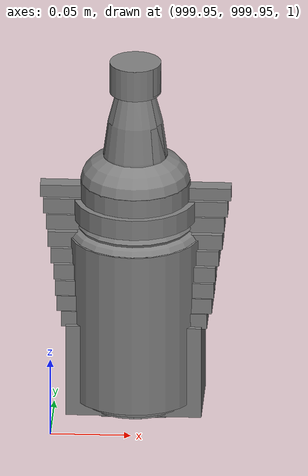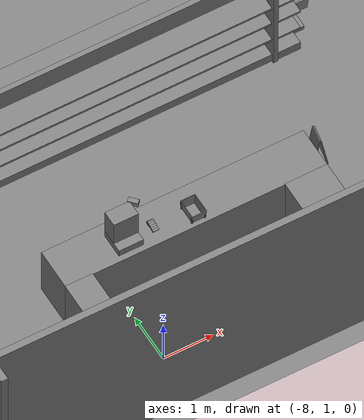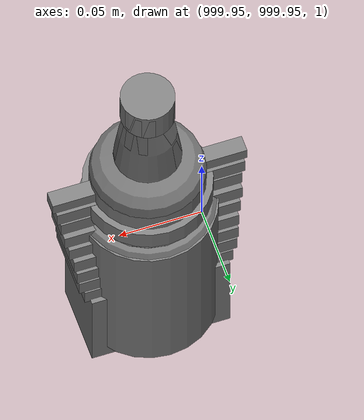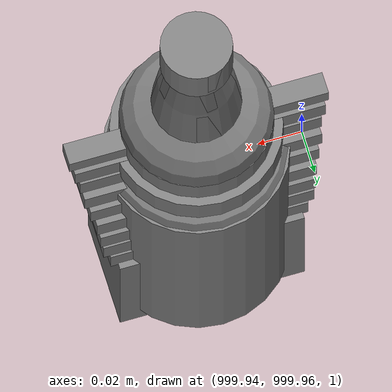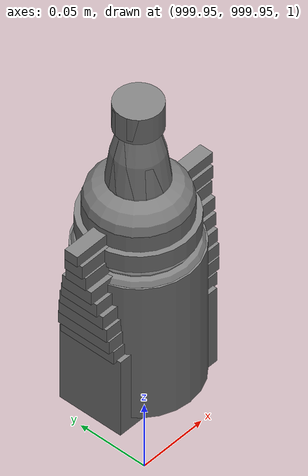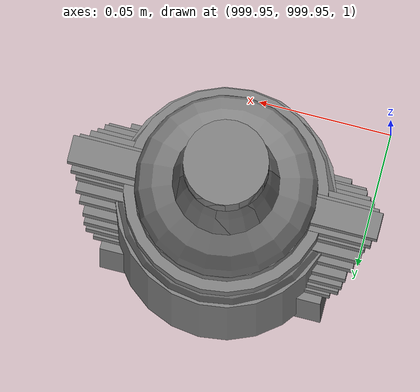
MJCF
<mujoco>
    <option gravity="0.000000000 0.000000000 -9.810000420" timestep="0.0166666" integrator="implicitfast" density="1.225" viscosity="1.8000001e-05" noslip_iterations="10" iterations="100" sdf_iterations="50">
        <flag multiccd="disable"/>
    </option>
    <size memory="1000M"/>
    <compiler coordinate="local"/>
    <worldbody>
        <light cutoff="30" pos="0 1 1" dir="0 -1 -2"/>
        <light cutoff="30" pos="0 -1 1" dir="0 1 -2"/>
        <body pos="-2.436573029 6.404376507 0.137849092" euler="0.000000000 0.000000000 0.000000000" name="openloong_gripper_2f85_fix_base_usda_shoppingtrolley_01">
            <geom contype="1" conaffinity="1" density="1000" type="box" material="" rgba="0.500000000 0.500000000 0.500000000 1.000000000" solimp="0.899999976 0.949999988 0.001000000" friction="1.000000000 0.005000000 0.000100000" solref="0.020000000 1.000000000" margin="0" condim="3" group="0" pos="-0.169898406 -0.178061336 0.864131629" quat="0.916343808 -0.400392294 -0.000000045 0.000000030" size="0.017999999 0.022499999 0.089999996" name="openloong_gripper_2f85_fix_base_usda_geom_A100E45E_50A1_463E_8C2F_86B90C9C341D"/>
            <geom contype="1" conaffinity="1" density="1000" type="box" material="" rgba="0.500000000 0.500000000 0.500000000 1.000000000" solimp="0.899999976 0.949999988 0.001000000" friction="1.000000000 0.005000000 0.000100000" solref="0.020000000 1.000000000" margin="0" condim="3" group="0" pos="-0.107458733 0.238907143 0.911498845" quat="0.634576976 0.622505128 -0.330067992 -0.317575932" size="0.017999999 0.022499999 0.035999998" name="openloong_gripper_2f85_fix_base_usda_geom_6B0349C3_F270_4063_94BD_CA5B06EB2AF4"/>
            <geom contype="1" conaffinity="1" density="1000" type="box" material="" rgba="0.500000000 0.500000000 0.500000000 1.000000000" solimp="0.899999976 0.949999988 0.001000000" friction="1.000000000 0.005000000 0.000100000" solref="0.020000000 1.000000000" margin="0" condim="3" group="0" pos="-0.005004787 0.248085022 0.912686050" quat="1.000000000 0.000000000 0.000000000 0.000000000" size="0.107999995 0.022499999 0.022499999" name="openloong_gripper_2f85_fix_base_usda_geom_1B80EED0_D663_414A_A479_83780A56FF63"/>
            <geom contype="1" conaffinity="1" density="1000" type="box" material="" rgba="0.500000000 0.500000000 0.500000000 1.000000000" solimp="0.899999976 0.949999988 0.001000000" friction="1.000000000 0.005000000 0.000100000" solref="0.020000000 1.000000000" margin="0" condim="3" group="0" pos="0.131482959 -0.182533979 0.598989725" quat="0.996607125 0.055331629 0.059003670 0.015205893" size="0.013499999 0.287999988 0.053999998" name="openloong_gripper_2f85_fix_base_usda_geom_80294EEC_D8EC_4174_B4C0_E1C27A2449FD"/>
            <geom contype="1" conaffinity="1" density="1000" type="box" material="" rgba="0.500000000 0.500000000 0.500000000 1.000000000" solimp="0.899999976 0.949999988 0.001000000" friction="1.000000000 0.005000000 0.000100000" solref="0.020000000 1.000000000" margin="0" condim="3" group="0" pos="-0.000005364 0.100332208 0.734785020" quat="0.999668717 0.025737956 -0.000000010 0.000000000" size="0.135000005 0.019800000 0.152999997" name="openloong_gripper_2f85_fix_base_usda_geom_49350DD8_3A1A_4FF5_8792_0D8FDE05668A"/>
            <geom contype="1" conaffinity="1" density="1000" type="box" material="" rgba="0.500000000 0.500000000 0.500000000 1.000000000" solimp="0.899999976 0.949999988 0.001000000" friction="1.000000000 0.005000000 0.000100000" solref="0.020000000 1.000000000" margin="0" condim="3" group="0" pos="-0.126757339 -0.182533979 0.598989725" quat="0.996607184 0.055331606 -0.059003651 -0.015205891" size="0.013499999 0.287999988 0.053999998" name="openloong_gripper_2f85_fix_base_usda_geom_808BE0CE_AF39_47A3_AAF5_E9985DDD26D8"/>
            <geom contype="1" conaffinity="1" density="1000" type="box" material="" rgba="0.500000000 0.500000000 0.500000000 1.000000000" solimp="0.899999976 0.949999988 0.001000000" friction="1.000000000 0.005000000 0.000100000" solref="0.020000000 1.000000000" margin="0" condim="3" group="0" pos="-0.134013891 0.200098798 0.912192523" quat="0.694057047 0.679413557 -0.172947660 -0.163618833" size="0.017999999 0.022499999 0.035999998" name="openloong_gripper_2f85_fix_base_usda_geom_D46C84A9_FAA0_465C_9376_D58A361B0862"/>
            <geom contype="1" conaffinity="1" density="1000" type="box" material="" rgba="0.500000000 0.500000000 0.500000000 1.000000000" solimp="0.899999976 0.949999988 0.001000000" friction="1.000000000 0.005000000 0.000100000" solref="0.020000000 1.000000000" margin="0" condim="3" group="0" pos="0.141839072 -0.191051379 0.702451229" quat="0.997147262 0.056065105 0.045779929 0.021407485" size="0.013499999 0.287999988 0.053999998" name="openloong_gripper_2f85_fix_base_usda_geom_F06BF813_4FF1_44DB_8B63_444BD84ED9A2"/>
            <geom contype="1" conaffinity="1" density="1000" type="box" material="" rgba="0.500000000 0.500000000 0.500000000 1.000000000" solimp="0.899999976 0.949999988 0.001000000" friction="1.000000000 0.005000000 0.000100000" solref="0.020000000 1.000000000" margin="0" condim="3" group="0" pos="-0.135714188 -0.191051379 0.694841146" quat="0.997147322 0.056064609 -0.045779683 -0.021407485" size="0.013499999 0.287999988 0.053999998" name="openloong_gripper_2f85_fix_base_usda_geom_342FE95E_A366_4FD4_ADDD_CB909B6122C0"/>
            <geom contype="1" conaffinity="1" density="1000" type="box" material="" rgba="0.500000000 0.500000000 0.500000000 1.000000000" solimp="0.899999976 0.949999988 0.001000000" friction="1.000000000 0.005000000 0.000100000" solref="0.020000000 1.000000000" margin="0" condim="3" group="0" pos="-0.000004721 -0.174527690 0.560063601" quat="0.996704638 0.081116498 -0.000000004 0.000000000" size="0.126000002 0.287999988 0.009000000" name="openloong_gripper_2f85_fix_base_usda_geom_062B4623_AF02_439C_BE5B_19D49356F79A"/>
            <geom contype="1" conaffinity="1" density="1000" type="box" material="" rgba="0.500000000 0.500000000 0.500000000 1.000000000" solimp="0.899999976 0.949999988 0.001000000" friction="1.000000000 0.005000000 0.000100000" solref="0.020000000 1.000000000" margin="0" condim="3" group="0" pos="0.134013891 0.200098798 0.912192523" quat="0.692574680 -0.680924535 -0.166899428 0.169783980" size="0.017999999 0.022499999 0.035999998" name="openloong_gripper_2f85_fix_base_usda_geom_F0C95DAC_8A4A_45D4_BAA5_70FE3F6945FF"/>
            <geom contype="1" conaffinity="1" density="1000" type="box" material="" rgba="0.500000000 0.500000000 0.500000000 1.000000000" solimp="0.899999976 0.949999988 0.001000000" friction="1.000000000 0.005000000 0.000100000" solref="0.020000000 1.000000000" margin="0" condim="3" group="0" pos="-0.012634277 -0.174527690 -0.088243507" quat="1.000000000 0.000000000 -0.000000004 0.000000000" size="0.135000005 0.287999988 0.044999998" name="openloong_gripper_2f85_fix_base_usda_geom_0F274C96_B2A3_456C_B122_57E4A7A1D2B4"/>
            <geom contype="1" conaffinity="1" density="1000" type="box" material="" rgba="0.500000000 0.500000000 0.500000000 1.000000000" solimp="0.899999976 0.949999988 0.001000000" friction="1.000000000 0.005000000 0.000100000" solref="0.020000000 1.000000000" margin="0" condim="3" group="0" pos="-0.142927840 -0.199506134 0.784674108" quat="0.998421252 0.016904408 -0.027109101 -0.046199299" size="0.013499999 0.305999994 0.063000001" name="openloong_gripper_2f85_fix_base_usda_geom_6B38551B_EB92_46A6_A131_EDA0C0FBCAD1"/>
            <geom contype="1" conaffinity="1" density="1000" type="box" material="" rgba="0.500000000 0.500000000 0.500000000 1.000000000" solimp="0.899999976 0.949999988 0.001000000" friction="1.000000000 0.005000000 0.000100000" solref="0.020000000 1.000000000" margin="0" condim="3" group="0" pos="-0.169898406 -0.043119621 0.915120542" quat="0.687021017 0.726584017 -0.005590606 -0.006832919" size="0.017999999 0.022499999 0.089999996" name="openloong_gripper_2f85_fix_base_usda_geom_C644D109_CDB2_4786_ACD9_F32348884486"/>
            <geom contype="1" conaffinity="1" density="1000" type="box" material="" rgba="0.500000000 0.500000000 0.500000000 1.000000000" solimp="0.899999976 0.949999988 0.001000000" friction="1.000000000 0.005000000 0.000100000" solref="0.020000000 1.000000000" margin="0" condim="3" group="0" pos="-0.000006008 -0.484932661 0.670727849" quat="0.997585475 0.069449045 -0.000000004 -0.000000089" size="0.179999992 0.013499999 0.170999989" name="openloong_gripper_2f85_fix_base_usda_geom_298FF899_5589_4BC5_9239_5611D37880C7"/>
            <geom contype="1" conaffinity="1" density="1000" type="box" material="" rgba="0.500000000 0.500000000 0.500000000 1.000000000" solimp="0.899999976 0.949999988 0.001000000" friction="1.000000000 0.005000000 0.000100000" solref="0.020000000 1.000000000" margin="0" condim="3" group="0" pos="0.160832971 0.103427693 0.910528183" quat="0.711112797 -0.700149298 -0.042821646 0.047705106" size="0.017999999 0.022499999 0.071999997" name="openloong_gripper_2f85_fix_base_usda_geom_E04DC715_298D_4BE0_A059_0B4E84B6D99F"/>
            <geom contype="1" conaffinity="1" density="1000" type="box" material="" rgba="0.500000000 0.500000000 0.500000000 1.000000000" solimp="0.899999976 0.949999988 0.001000000" friction="1.000000000 0.005000000 0.000100000" solref="0.020000000 1.000000000" margin="0" condim="3" group="0" pos="-0.160832763 0.103427693 0.910528183" quat="0.711469591 0.699786782 -0.048386075 -0.042050660" size="0.017999999 0.022499999 0.071999997" name="openloong_gripper_2f85_fix_base_usda_geom_58B0CDEC_C16A_4B78_B4AB_FC74D9E51924"/>
            <geom contype="1" conaffinity="1" density="1000" type="box" material="" rgba="0.500000000 0.500000000 0.500000000 1.000000000" solimp="0.899999976 0.949999988 0.001000000" friction="1.000000000 0.005000000 0.000100000" solref="0.020000000 1.000000000" margin="0" condim="3" group="0" pos="0.169898629 -0.178061336 0.864131629" quat="0.916343808 -0.400392294 -0.000000045 0.000000030" size="0.017999999 0.022499999 0.089999996" name="openloong_gripper_2f85_fix_base_usda_geom_72A6668B_1EB3_4AFC_8A8C_88559879CCED"/>
            <geom contype="1" conaffinity="1" density="1000" type="box" material="" rgba="0.500000000 0.500000000 0.500000000 1.000000000" solimp="0.899999976 0.949999988 0.001000000" friction="1.000000000 0.005000000 0.000100000" solref="0.020000000 1.000000000" margin="0" condim="3" group="0" pos="0.103667587 0.233050480 0.912927270" quat="0.634205043 -0.622199059 -0.324503720 0.324576139" size="0.017999999 0.022499999 0.035999998" name="openloong_gripper_2f85_fix_base_usda_geom_A4AE5180_52E3_48F1_B295_723A6562869C"/>
            <geom contype="1" conaffinity="1" density="1000" type="box" material="" rgba="0.500000000 0.500000000 0.500000000 1.000000000" solimp="0.899999976 0.949999988 0.001000000" friction="1.000000000 0.005000000 0.000100000" solref="0.020000000 1.000000000" margin="0" condim="3" group="0" pos="0.169898629 -0.043119621 0.915120542" quat="0.687029123 -0.726576388 -0.006509603 0.005963952" size="0.017999999 0.022499999 0.089999996" name="openloong_gripper_2f85_fix_base_usda_geom_0BDC5B56_A586_4996_BC62_4F015B1B2E3E"/>
            <geom contype="1" conaffinity="1" density="1000" type="box" material="" rgba="0.500000000 0.500000000 0.500000000 1.000000000" solimp="0.899999976 0.949999988 0.001000000" friction="1.000000000 0.005000000 0.000100000" solref="0.020000000 1.000000000" margin="0" condim="3" group="0" pos="0.148195267 -0.199506566 0.782808602" quat="0.998808920 0.017156634 0.026950166 0.036880098" size="0.013499999 0.305999994 0.063000001" name="openloong_gripper_2f85_fix_base_usda_geom_05817EEB_DF0F_4A77_BA60_8D269DC7C1B8"/>
            <freejoint name="openloong_gripper_2f85_fix_base_usda_shoppingtrolley_01_joint"/>
            <site size="0.005000000 0.005000000 0.005000000" rgba="0.500000000 0.500000000 0.500000000 1.000000000" pos="0.000000000 0.000000000 0.000000000" quat="1.000000000 0.000000000 0.000000000 0.000000000" group="0" type="sphere" name="openloong_gripper_2f85_fix_base_usda_shoppingtrolley_01"/>
        </body>
        <body pos="1000.000000000 1000.000000000 1.000000000" euler="0.000000000 0.000000000 0.000000000" name="openloong_gripper_2f85_fix_base_usda_can">
            <geom contype="1" conaffinity="1" density="1000" type="cylinder" material="" rgba="0.500000000 0.500000000 0.500000000 1.000000000" solimp="0.899999976 0.949999988 0.001000000" friction="1.000000000 0.005000000 0.000100000" solref="0.020000000 1.000000000" margin="0" condim="3" group="0" pos="0.000000000 0.000000000 0.079676986" quat="1.000000000 0.000000000 0.000000000 0.000000000" size="0.034000002 0.071999997 1.000000000" name="openloong_gripper_2f85_fix_base_usda_geom_964B7C16_C11A_40D4_972A_2E98B8E2AD11"/>
            <geom contype="1" conaffinity="1" density="1000" type="ellipsoid" material="" rgba="0.500000000 0.500000000 0.500000000 1.000000000" solimp="0.899999976 0.949999988 0.001000000" friction="1.000000000 0.005000000 0.000100000" solref="0.020000000 1.000000000" margin="0" condim="3" group="0" pos="0.000000000 0.000000000 0.151854277" quat="1.000000000 0.000000000 0.000000000 0.000000000" size="0.034000002 0.034000002 0.020000000" name="openloong_gripper_2f85_fix_base_usda_geom_F657C918_AD7C_4493_A232_066EFFF136C9"/>
            <geom contype="1" conaffinity="1" density="1000" type="box" material="" rgba="0.500000000 0.500000000 0.500000000 1.000000000" solimp="0.899999976 0.949999988 0.001000000" friction="1.000000000 0.005000000 0.000100000" solref="0.020000000 1.000000000" margin="0" condim="3" group="0" pos="0.000000000 0.000000000 0.004777670" quat="1.000000000 0.000000000 0.000000000 0.000000000" size="0.020000000 0.020000000 0.005000000" name="openloong_gripper_2f85_fix_base_usda_geom_1E9E7906_D0C9_4B04_BE26_956AA8C8DBA7"/>
            <freejoint name="openloong_gripper_2f85_fix_base_usda_can_joint"/>
            <site size="0.005000000 0.005000000 0.005000000" rgba="0.500000000 0.500000000 0.500000000 1.000000000" pos="0.000000000 0.000000000 0.000000000" quat="1.000000000 0.000000000 0.000000000 0.000000000" group="0" type="sphere" name="openloong_gripper_2f85_fix_base_usda_cansite"/>
        </body>
        <body pos="1000.000000000 1000.000000000 1.000000000" euler="0.000000000 0.000000000 0.000000000" name="openloong_gripper_2f85_fix_base_usda_salt">
            <geom contype="1" conaffinity="1" density="1000" type="box" material="" rgba="0.500000000 0.500000000 0.500000000 1.000000000" solimp="0.899999976 0.949999988 0.001000000" friction="1.000000000 0.005000000 0.000100000" solref="0.020000000 1.000000000" margin="0" condim="3" group="0" pos="0.000305176 0.000000000 0.084862232" quat="1.000000000 0.000000000 0.000000000 0.000000000" size="0.048999999 0.018999999 0.005000000" name="openloong_gripper_2f85_fix_base_usda_geom_C52F6059_9A2B_4020_B791_06DE242B8578"/>
            <geom contype="1" conaffinity="1" density="1000" type="box" material="" rgba="0.500000000 0.500000000 0.500000000 1.000000000" solimp="0.899999976 0.949999988 0.001000000" friction="1.000000000 0.005000000 0.000100000" solref="0.020000000 1.000000000" margin="0" condim="3" group="0" pos="0.000305176 0.000000000 0.104564309" quat="1.000000000 0.000000000 0.000000000 0.000000000" size="0.052000001 0.014000000 0.005000000" name="openloong_gripper_2f85_fix_base_usda_geom_004D9F28_EED7_48B4_BABF_ADE81DAD0296"/>
            <geom contype="1" conaffinity="1" density="1000" type="box" material="" rgba="0.500000000 0.500000000 0.500000000 1.000000000" solimp="0.899999976 0.949999988 0.001000000" friction="1.000000000 0.005000000 0.000100000" solref="0.020000000 1.000000000" margin="0" condim="3" group="0" pos="0.000305176 0.000000000 0.114487171" quat="1.000000000 0.000000000 0.000000000 0.000000000" size="0.054000001 0.011500000 0.005000000" name="openloong_gripper_2f85_fix_base_usda_geom_C1D72645_4E2E_4FEC_9BE0_5E6AAEDDAD49"/>
            <geom contype="1" conaffinity="1" density="1000" type="box" material="" rgba="0.500000000 0.500000000 0.500000000 1.000000000" solimp="0.899999976 0.949999988 0.001000000" friction="1.000000000 0.005000000 0.000100000" solref="0.020000000 1.000000000" margin="0" condim="3" group="0" pos="0.000305176 0.000000000 0.075103164" quat="1.000000000 0.000000000 0.000000000 0.000000000" size="0.048000000 0.020000000 0.005000000" name="openloong_gripper_2f85_fix_base_usda_geom_1415C340_928A_4228_A2BC_2763CE2DFF1D"/>
            <geom contype="1" conaffinity="1" density="1000" type="box" material="" rgba="0.500000000 0.500000000 0.500000000 1.000000000" solimp="0.899999976 0.949999988 0.001000000" friction="1.000000000 0.005000000 0.000100000" solref="0.020000000 1.000000000" margin="0" condim="3" group="0" pos="0.000305176 0.000000000 0.134892464" quat="1.000000000 0.000000000 0.000000000 0.000000000" size="0.057000000 0.007000000 0.005000000" name="openloong_gripper_2f85_fix_base_usda_geom_1E26962D_EE4C_4CB3_B3F0_7ABC4CC3C630"/>
            <geom contype="1" conaffinity="1" density="1000" type="box" material="" rgba="0.500000000 0.500000000 0.500000000 1.000000000" solimp="0.899999976 0.949999988 0.001000000" friction="1.000000000 0.005000000 0.000100000" solref="0.020000000 1.000000000" margin="0" condim="3" group="0" pos="0.000305176 0.000000000 0.094920278" quat="1.000000000 0.000000000 0.000000000 0.000000000" size="0.050000001 0.017000001 0.005000000" name="openloong_gripper_2f85_fix_base_usda_geom_A9AEDEB7_B3C6_4D32_965F_9F6ED13ADA83"/>
            <geom contype="1" conaffinity="1" density="1000" type="box" material="" rgba="0.500000000 0.500000000 0.500000000 1.000000000" solimp="0.899999976 0.949999988 0.001000000" friction="1.000000000 0.005000000 0.000100000" solref="0.020000000 1.000000000" margin="0" condim="3" group="0" pos="0.000305176 0.000000000 0.065204859" quat="1.000000000 0.000000000 0.000000000 0.000000000" size="0.045000002 0.021000000 0.005000000" name="openloong_gripper_2f85_fix_base_usda_geom_0BF96647_B5FA_4ABC_92F3_BDD727FA5131"/>
            <geom contype="1" conaffinity="1" density="1000" type="box" material="" rgba="0.500000000 0.500000000 0.500000000 1.000000000" solimp="0.899999976 0.949999988 0.001000000" friction="1.000000000 0.005000000 0.000100000" solref="0.020000000 1.000000000" margin="0" condim="3" group="0" pos="0.000305176 0.000000000 0.144135714" quat="1.000000000 0.000000000 0.000000000 0.000000000" size="0.059000000 0.005000000 0.004000000" name="openloong_gripper_2f85_fix_base_usda_geom_208C4550_8F3A_47E0_B394_785785707F35"/>
            <geom contype="1" conaffinity="1" density="1000" type="box" material="" rgba="0.500000000 0.500000000 0.500000000 1.000000000" solimp="0.899999976 0.949999988 0.001000000" friction="1.000000000 0.005000000 0.000100000" solref="0.020000000 1.000000000" margin="0" condim="3" group="0" pos="0.000000000 0.000000000 0.031593561" quat="1.000000000 0.000000000 0.000000000 0.000000000" size="0.041999999 0.024000000 0.029999999" name="openloong_gripper_2f85_fix_base_usda_geom_643802FC_66A1_4A62_9F9C_CFE2871DF3BB"/>
            <geom contype="1" conaffinity="1" density="1000" type="box" material="" rgba="0.500000000 0.500000000 0.500000000 1.000000000" solimp="0.899999976 0.949999988 0.001000000" friction="1.000000000 0.005000000 0.000100000" solref="0.020000000 1.000000000" margin="0" condim="3" group="0" pos="0.000305176 0.000000000 0.124608755" quat="1.000000000 0.000000000 0.000000000 0.000000000" size="0.055000000 0.008000000 0.005000000" name="openloong_gripper_2f85_fix_base_usda_geom_09C4EB9D_18C2_4CEF_B79B_51FFAAD220EB"/>
            <freejoint name="openloong_gripper_2f85_fix_base_usda_salt_joint"/>
            <site size="0.005000000 0.005000000 0.005000000" rgba="0.500000000 0.500000000 0.500000000 1.000000000" pos="0.000000000 0.000000000 0.000000000" quat="1.000000000 0.000000000 0.000000000 0.000000000" group="0" type="sphere" name="openloong_gripper_2f85_fix_base_usda_saltsite"/>
        </body>
        <body pos="1000.000000000 1000.000000000 1.000000000" euler="0.000000000 0.000000000 0.000000000" name="openloong_gripper_2f85_fix_base_usda_bottle_red">
            <geom contype="1" conaffinity="1" density="1000" type="ellipsoid" material="" rgba="0.500000000 0.500000000 0.500000000 1.000000000" solimp="0.899999976 0.949999988 0.001000000" friction="1.000000000 0.005000000 0.000100000" solref="0.020000000 1.000000000" margin="0" condim="3" group="0" pos="0.000000000 0.000000000 0.144284487" quat="1.000000000 0.000000000 0.000000000 0.000000000" size="0.021000000 0.021000000 0.079999998" name="openloong_gripper_2f85_fix_base_usda_geom_3EC27B92_B7FA_4722_BBF9_71E827550F33"/>
            <geom contype="1" conaffinity="1" density="1000" type="cylinder" material="" rgba="0.500000000 0.500000000 0.500000000 1.000000000" solimp="0.899999976 0.949999988 0.001000000" friction="1.000000000 0.005000000 0.000100000" solref="0.020000000 1.000000000" margin="0" condim="3" group="0" pos="0.000000000 0.000000000 0.220618963" quat="1.000000000 0.000000000 0.000000000 0.000000000" size="0.016000001 0.010000000 1.000000000" name="openloong_gripper_2f85_fix_base_usda_geom_B18A29B4_F896_4550_A123_7AFD6B47A7EB"/>
            <geom contype="1" conaffinity="1" density="1000" type="ellipsoid" material="" rgba="0.500000000 0.500000000 0.500000000 1.000000000" solimp="0.899999976 0.949999988 0.001000000" friction="1.000000000 0.005000000 0.000100000" solref="0.020000000 1.000000000" margin="0" condim="3" group="0" pos="0.000000000 0.000000000 0.118945479" quat="1.000000000 0.000000000 0.000000000 0.000000000" size="0.030999999 0.030999999 0.029999999" name="openloong_gripper_2f85_fix_base_usda_geom_F6940D62_F8B8_41E0_A83E_208212F19717"/>
            <geom contype="1" conaffinity="1" density="1000" type="box" material="" rgba="0.500000000 0.500000000 0.500000000 1.000000000" solimp="0.899999976 0.949999988 0.001000000" friction="1.000000000 0.005000000 0.000100000" solref="0.020000000 1.000000000" margin="0" condim="3" group="0" pos="0.000000000 0.000000000 0.002189159" quat="1.000000000 0.000000000 0.000000000 0.000000000" size="0.020000000 0.020000000 0.003000000" name="openloong_gripper_2f85_fix_base_usda_geom_BC83223B_3B03_4500_8771_3B4D7CA7C8FD"/>
            <geom contype="1" conaffinity="1" density="1000" type="cylinder" material="" rgba="0.500000000 0.500000000 0.500000000 1.000000000" solimp="0.899999976 0.949999988 0.001000000" friction="1.000000000 0.005000000 0.000100000" solref="0.020000000 1.000000000" margin="0" condim="3" group="0" pos="0.000000000 -0.000366211 0.060884237" quat="1.000000000 0.000000000 0.000000000 0.000000000" size="0.030999999 0.057999998 1.000000000" name="openloong_gripper_2f85_fix_base_usda_geom_0C7EF22F_A224_49D4_837A_728B08913817"/>
            <freejoint name="openloong_gripper_2f85_fix_base_usda_bottle_red_joint"/>
            <site size="0.005000000 0.005000000 0.005000000" rgba="0.500000000 0.500000000 0.500000000 1.000000000" pos="0.000000000 0.000000000 0.000000000" quat="0.999961913 0.008726535 0.000000000 0.000000000" group="0" type="sphere" name="openloong_gripper_2f85_fix_base_usda_bottle_redsite"/>
        </body>
        <body pos="-2.320804596 6.621684551 1.797480345" euler="-156.954818726 -34.511543274 -29.722085953" mocap="true" name="spotlight1_SpotLight"/>
        <body pos="1000.000000000 1000.000000000 1.000000000" euler="0.000000000 0.000000000 0.000000000" name="openloong_gripper_2f85_fix_base_usda_jar_01">
            <geom contype="1" conaffinity="1" density="1000" type="box" material="" rgba="0.500000000 0.500000000 0.500000000 1.000000000" solimp="0.899999976 0.949999988 0.001000000" friction="1.000000000 0.005000000 0.000100000" solref="0.020000000 1.000000000" margin="0" condim="3" group="0" pos="0.000000000 0.000000000 0.006158113" quat="1.000000000 0.000000000 0.000000000 0.000000000" size="0.020000000 0.020000000 0.005000000" name="openloong_gripper_2f85_fix_base_usda_geom_C56EA784_FCA7_41A7_9C0D_0A840DCE255D"/>
            <geom contype="1" conaffinity="1" density="1000" type="cylinder" material="" rgba="0.500000000 0.500000000 0.500000000 1.000000000" solimp="0.899999976 0.949999988 0.001000000" friction="1.000000000 0.005000000 0.000100000" solref="0.020000000 1.000000000" margin="0" condim="3" group="0" pos="0.000000000 0.000000000 0.062744498" quat="1.000000000 0.000000000 0.000000000 0.000000000" size="0.041000001 0.052999999 1.000000000" name="openloong_gripper_2f85_fix_base_usda_geom_B36612A3_54C7_497B_9F0F_D62BA19E566B"/>
            <geom contype="1" conaffinity="1" density="1000" type="ellipsoid" material="" rgba="0.500000000 0.500000000 0.500000000 1.000000000" solimp="0.899999976 0.949999988 0.001000000" friction="1.000000000 0.005000000 0.000100000" solref="0.020000000 1.000000000" margin="0" condim="3" group="0" pos="0.000000000 0.000000000 0.122252703" quat="1.000000000 0.000000000 0.000000000 0.000000000" size="0.035999998 0.035999998 0.010000000" name="openloong_gripper_2f85_fix_base_usda_geom_CD3855DC_EEDD_467C_9F00_4A4C465B6E7A"/>
            <geom contype="1" conaffinity="1" density="1000" type="cylinder" material="" rgba="0.500000000 0.500000000 0.500000000 1.000000000" solimp="0.899999976 0.949999988 0.001000000" friction="1.000000000 0.005000000 0.000100000" solref="0.020000000 1.000000000" margin="0" condim="3" group="0" pos="0.000000000 0.000000000 0.015747190" quat="1.000000000 0.000000000 0.000000000 0.000000000" size="0.035000000 0.010000000 1.000000000" name="openloong_gripper_2f85_fix_base_usda_geom_BF02958D_0A07_4A6C_AAC8_3EFEE0174C91"/>
            <geom contype="1" conaffinity="1" density="1000" type="ellipsoid" material="" rgba="0.500000000 0.500000000 0.500000000 1.000000000" solimp="0.899999976 0.949999988 0.001000000" friction="1.000000000 0.005000000 0.000100000" solref="0.020000000 1.000000000" margin="0" condim="3" group="0" pos="0.000000000 0.000000000 0.115815401" quat="1.000000000 0.000000000 0.000000000 0.000000000" size="0.039999999 0.039999999 0.010000000" name="openloong_gripper_2f85_fix_base_usda_geom_670BADE4_6DBC_4F7E_84D3_7F57803B4E38"/>
            <geom contype="1" conaffinity="1" density="1000" type="cylinder" material="" rgba="0.500000000 0.500000000 0.500000000 1.000000000" solimp="0.899999976 0.949999988 0.001000000" friction="1.000000000 0.005000000 0.000100000" solref="0.020000000 1.000000000" margin="0" condim="3" group="0" pos="0.000000000 0.000000000 0.133183479" quat="1.000000000 0.000000000 0.000000000 0.000000000" size="0.037999999 0.006500000 1.000000000" name="openloong_gripper_2f85_fix_base_usda_geom_AE8DA44A_82E6_48DD_A337_21C0DC1E75D5"/>
            <freejoint name="openloong_gripper_2f85_fix_base_usda_jar_01_joint"/>
            <site size="0.005000000 0.005000000 0.005000000" rgba="0.500000000 0.500000000 0.500000000 1.000000000" pos="0.000000000 0.000000000 0.000000000" quat="1.000000000 0.000000000 0.000000000 0.000000000" group="0" type="sphere" name="openloong_gripper_2f85_fix_base_usda_jar_01site"/>
        </body>
        <body pos="1000.000000000 1000.000000000 1.000000000" euler="0.000000000 0.000000000 0.000000000" name="openloong_gripper_2f85_fix_base_usda_bottle_blue">
            <geom contype="1" conaffinity="1" density="1000" type="ellipsoid" material="" rgba="0.500000000 0.500000000 0.500000000 1.000000000" solimp="0.899999976 0.949999988 0.001000000" friction="1.000000000 0.005000000 0.000100000" solref="0.020000000 1.000000000" margin="0" condim="3" group="0" pos="0.000000000 0.000000000 0.118920922" quat="1.000000000 0.000000000 0.000000000 0.000000000" size="0.030999999 0.030999999 0.029999999" name="openloong_gripper_2f85_fix_base_usda_geom_04510945_FA0E_44BA_A68C_640D82D9956A"/>
            <geom contype="1" conaffinity="1" density="1000" type="box" material="" rgba="0.500000000 0.500000000 0.500000000 1.000000000" solimp="0.899999976 0.949999988 0.001000000" friction="1.000000000 0.005000000 0.000100000" solref="0.020000000 1.000000000" margin="0" condim="3" group="0" pos="0.000000000 0.000000000 0.002164602" quat="1.000000000 0.000000000 0.000000000 0.000000000" size="0.020000000 0.020000000 0.003000000" name="openloong_gripper_2f85_fix_base_usda_geom_F0B201E3_8767_4EA3_AC92_6F2E9109C327"/>
            <geom contype="1" conaffinity="1" density="1000" type="cylinder" material="" rgba="0.500000000 0.500000000 0.500000000 1.000000000" solimp="0.899999976 0.949999988 0.001000000" friction="1.000000000 0.005000000 0.000100000" solref="0.020000000 1.000000000" margin="0" condim="3" group="0" pos="0.000000000 -0.000366211 0.060859680" quat="1.000000000 0.000000000 0.000000000 0.000000000" size="0.030999999 0.057999998 1.000000000" name="openloong_gripper_2f85_fix_base_usda_geom_EAFF7E97_B446_4A66_B0F3_06351AD196A5"/>
            <geom contype="1" conaffinity="1" density="1000" type="cylinder" material="" rgba="0.500000000 0.500000000 0.500000000 1.000000000" solimp="0.899999976 0.949999988 0.001000000" friction="1.000000000 0.005000000 0.000100000" solref="0.020000000 1.000000000" margin="0" condim="3" group="0" pos="0.000000000 0.000000000 0.220594406" quat="1.000000000 0.000000000 0.000000000 0.000000000" size="0.016000001 0.010000000 1.000000000" name="openloong_gripper_2f85_fix_base_usda_geom_275DA377_67BF_4D2E_B87C_D043D630316E"/>
            <geom contype="1" conaffinity="1" density="1000" type="ellipsoid" material="" rgba="0.500000000 0.500000000 0.500000000 1.000000000" solimp="0.899999976 0.949999988 0.001000000" friction="1.000000000 0.005000000 0.000100000" solref="0.020000000 1.000000000" margin="0" condim="3" group="0" pos="0.000000000 0.000000000 0.144259930" quat="1.000000000 0.000000000 0.000000000 0.000000000" size="0.021000000 0.021000000 0.079999998" name="openloong_gripper_2f85_fix_base_usda_geom_E78C0C76_E06D_40C4_A4CA_058572A5BB84"/>
            <freejoint name="openloong_gripper_2f85_fix_base_usda_bottle_blue_joint"/>
            <site size="0.005000000 0.005000000 0.005000000" rgba="0.500000000 0.500000000 0.500000000 1.000000000" pos="0.000000000 0.000000000 0.000000000" quat="0.999961913 0.008726535 0.000000000 0.000000000" group="0" type="sphere" name="openloong_gripper_2f85_fix_base_usda_bottle_bluesite"/>
        </body>
        <body pos="-1.896624446 5.764784336 1.717980742" euler="-26.060504913 -6.748805523 -68.106643677" mocap="true" name="spotlight3_SpotLight"/>
        <body pos="-2.280745745 5.941706657 1.662275314" euler="-121.904373169 33.046485901 -58.406372070" mocap="true" name="spotlight6_SpotLight"/>
        <body pos="0.000000000 0.000000000 0.000000000" euler="0.000000000 0.000000000 0.000000000" name=" Static Objects_ Static Objects">
            <geom contype="1" conaffinity="1" density="1000" type="box" material="" rgba="0.500000000 0.500000000 0.500000000 1.000000000" solimp="0.899999976 0.949999988 0.001000000" friction="1.000000000 0.005000000 0.000100000" solref="0.020000000 1.000000000" margin="0" condim="3" group="0" pos="-3.101639986 6.150595188 1.018643856" quat="1.000000000 0.000000000 0.000000000 0.000000000" size="0.050000001 0.579999983 1.019999981" name=" Static Objects_geom_3251C197_CC10_4B86_87FF_FE574293DF3C"/>
            <geom contype="1" conaffinity="1" density="1000" type="box" material="" rgba="0.500000000 0.500000000 0.500000000 1.000000000" solimp="0.899999976 0.949999988 0.001000000" friction="1.000000000 0.005000000 0.000100000" solref="0.020000000 1.000000000" margin="0" condim="3" group="0" pos="-2.825197220 6.153595448 1.115278244" quat="0.707107067 0.000000000 0.000000000 0.707106471" size="0.550000012 0.239999995 0.025000000" name=" Static Objects_geom_D473ACFB_90E1_4B66_B5F5_8809F1F6878D"/>
            <geom contype="1" conaffinity="1" density="1000" type="box" material="" rgba="0.500000000 0.500000000 0.500000000 1.000000000" solimp="0.899999976 0.949999988 0.001000000" friction="1.000000000 0.005000000 0.000100000" solref="0.020000000 1.000000000" margin="0" condim="3" group="0" pos="-2.825197220 6.153595448 0.097434282" quat="0.707107067 0.000000000 0.000000000 0.707106471" size="0.550000012 0.239999995 0.098999999" name=" Static Objects_geom_84AA33CA_8019_454B_977E_297A0E1A184D"/>
            <geom contype="1" conaffinity="1" density="1000" type="box" material="" rgba="0.500000000 0.500000000 0.500000000 1.000000000" solimp="0.899999976 0.949999988 0.001000000" friction="1.000000000 0.005000000 0.000100000" solref="0.020000000 1.000000000" margin="0" condim="3" group="0" pos="-6.293097973 6.153595448 1.114443064" quat="0.707107067 0.000000000 0.000000000 0.707106471" size="0.529999971 3.134999990 0.025000000" name=" Static Objects_geom_FCFBAEFC_5F30_4DEA_9C33_314690C9EA6C"/>
            <geom contype="1" conaffinity="1" density="1000" type="box" material="" rgba="0.500000000 0.500000000 0.500000000 1.000000000" solimp="0.899999976 0.949999988 0.001000000" friction="1.000000000 0.005000000 0.000100000" solref="0.020000000 1.000000000" margin="0" condim="3" group="0" pos="-6.286010742 6.153595448 0.096129179" quat="0.707107067 0.000000000 0.000000000 0.707106471" size="0.529999971 3.134999990 0.098999999" name=" Static Objects_geom_46BFF856_44A5_4BCC_8ACC_7E98147C9C83"/>
            <geom contype="1" conaffinity="1" density="1000" type="box" material="" rgba="0.500000000 0.500000000 0.500000000 1.000000000" solimp="0.899999976 0.949999988 0.001000000" friction="1.000000000 0.005000000 0.000100000" solref="0.020000000 1.000000000" margin="0" condim="3" group="0" pos="-2.825197220 6.153595448 1.563861728" quat="0.707107067 0.000000000 0.000000000 0.707106471" size="0.550000012 0.239999995 0.025000000" name=" Static Objects_geom_D32B89CC_C7FC_45AD_90E1_87DF97C774CC"/>
            <geom contype="1" conaffinity="1" density="1000" type="box" material="" rgba="0.500000000 0.500000000 0.500000000 1.000000000" solimp="0.899999976 0.949999988 0.001000000" friction="1.000000000 0.005000000 0.000100000" solref="0.020000000 1.000000000" margin="0" condim="3" group="0" pos="-6.311686516 6.153595448 1.018643856" quat="0.707107067 0.000000000 0.000000000 0.707106471" size="0.050000001 3.150000095 1.019999981" name=" Static Objects_geom_99864C59_07C3_4E52_BC32_63C0A3E73074"/>
            <geom contype="1" conaffinity="1" density="1000" type="box" material="" rgba="0.500000000 0.500000000 0.500000000 1.000000000" solimp="0.899999976 0.949999988 0.001000000" friction="1.000000000 0.005000000 0.000100000" solref="0.020000000 1.000000000" margin="0" condim="3" group="0" pos="-2.825197220 6.153595448 0.629031777" quat="0.707107067 0.000000000 0.000000000 0.707106471" size="0.550000012 0.239999995 0.025000000" name=" Static Objects_geom_B8128CEC_DCB7_4159_AC82_F36ADC6B860D"/>
            <geom contype="1" conaffinity="1" density="1000" type="box" material="" rgba="0.500000000 0.500000000 0.500000000 1.000000000" solimp="0.899999976 0.949999988 0.001000000" friction="1.000000000 0.005000000 0.000100000" solref="0.020000000 1.000000000" margin="0" condim="3" group="0" pos="-6.286010742 6.153595448 1.563861728" quat="0.707107067 0.000000000 0.000000000 0.707106471" size="0.529999971 3.134999990 0.025000000" name=" Static Objects_geom_53349787_87BF_442F_AD82_F22547ABB446"/>
            <geom contype="1" conaffinity="1" density="1000" type="box" material="" rgba="0.500000000 0.500000000 0.500000000 1.000000000" solimp="0.899999976 0.949999988 0.001000000" friction="1.000000000 0.005000000 0.000100000" solref="0.020000000 1.000000000" margin="0" condim="3" group="0" pos="-6.286010742 6.153595448 0.629031777" quat="0.707107067 0.000000000 0.000000000 0.707106471" size="0.529999971 3.134999990 0.025000000" name=" Static Objects_geom_9E8770BC_1B3E_4B1F_8680_0D6B4F286035"/>
            <geom contype="1" conaffinity="1" density="1000" type="box" material="" rgba="0.500000000 0.500000000 0.500000000 1.000000000" solimp="0.899999976 0.949999988 0.001000000" friction="1.000000000 0.005000000 0.000100000" solref="0.020000000 1.000000000" margin="0" condim="3" group="0" pos="-7.719123363 2.867671013 1.173410416" quat="1.000000000 0.000000000 0.000000000 0.000000000" size="0.250000000 0.250000000 0.079999998" name=" Static Objects_geom_12868FE9_F070_45F8_8204_E05ECAA62F1F"/>
            <geom contype="1" conaffinity="1" density="1000" type="box" material="" rgba="0.500000000 0.500000000 0.500000000 1.000000000" solimp="0.899999976 0.949999988 0.001000000" friction="1.000000000 0.005000000 0.000100000" solref="0.020000000 1.000000000" margin="0" condim="3" group="0" pos="-7.408766270 3.088089943 1.776644945" quat="0.928051054 0.000000000 0.000000000 0.372453064" size="0.050000001 0.100000001 0.050000001" name=" Static Objects_geom_62026A99_263C_44FC_9517_7E71A663D9A6"/>
            <geom contype="1" conaffinity="1" density="1000" type="box" material="" rgba="0.500000000 0.500000000 0.500000000 1.000000000" solimp="0.899999976 0.949999988 0.001000000" friction="1.000000000 0.005000000 0.000100000" solref="0.020000000 1.000000000" margin="0" condim="3" group="0" pos="-7.719123363 2.958004713 1.530241251" quat="1.000000000 0.000000000 0.000000000 0.000000000" size="0.250000000 0.159999996 0.280000001" name=" Static Objects_geom_74486756_8D5D_4FEB_BC06_A177EED0728A"/>
            <geom contype="1" conaffinity="1" density="1000" type="cylinder" material="" rgba="0.500000000 0.500000000 0.500000000 1.000000000" solimp="0.899999976 0.949999988 0.001000000" friction="1.000000000 0.005000000 0.000100000" solref="0.020000000 1.000000000" margin="0" condim="3" group="0" pos="-7.427312374 3.069516420 1.502544641" quat="0.928051054 0.000000000 0.000000000 0.372453064" size="0.015000000 0.230000004 0.100000001" name=" Static Objects_geom_234DF028_AC06_4635_812E_A054F5101BCD"/>
            <geom contype="1" conaffinity="1" density="1000" type="box" material="" rgba="0.500000000 0.500000000 0.500000000 1.000000000" solimp="0.899999976 0.949999988 0.001000000" friction="1.000000000 0.005000000 0.000100000" solref="0.020000000 1.000000000" margin="0" condim="3" group="0" pos="-7.437745571 3.067511320 1.289965630" quat="1.000000000 0.000000000 0.000000000 0.000000000" size="0.029999999 0.020000000 0.020000000" name=" Static Objects_geom_1BA38BCA_F14C_4CA9_8AB4_EEA2772AEDFA"/>
            <geom contype="1" conaffinity="1" density="1000" type="box" material="" rgba="0.500000000 0.500000000 0.500000000 1.000000000" solimp="0.899999976 0.949999988 0.001000000" friction="1.000000000 0.005000000 0.000100000" solref="0.020000000 1.000000000" margin="0" condim="3" group="0" pos="-9.058088303 6.434794426 1.209077358" quat="1.000000000 0.000000000 0.000000000 0.000000000" size="0.250000000 0.100000001 0.070000000" name=" Static Objects_geom_4279A686_1693_4332_AD8F_1A55F8B25D57"/>
            <geom contype="1" conaffinity="1" density="1000" type="box" material="" rgba="0.500000000 0.500000000 0.500000000 1.000000000" solimp="0.899999976 0.949999988 0.001000000" friction="1.000000000 0.005000000 0.000100000" solref="0.020000000 1.000000000" margin="0" condim="3" group="0" pos="-7.886891365 6.459744930 0.352518857" quat="1.000000000 0.000000000 0.000000000 0.000000000" size="1.500000000 0.200000003 0.150000006" name=" Static Objects_geom_49A4894F_8CF5_40E8_9F8B_E54275F2FA6B"/>
            <geom contype="1" conaffinity="1" density="1000" type="box" material="" rgba="0.500000000 0.500000000 0.500000000 1.000000000" solimp="0.899999976 0.949999988 0.001000000" friction="1.000000000 0.005000000 0.000100000" solref="0.020000000 1.000000000" margin="0" condim="3" group="0" pos="-9.237723351 6.464855671 1.209077358" quat="1.000000000 0.000000000 0.000000000 0.000000000" size="0.100000001 0.100000001 0.070000000" name=" Static Objects_geom_CF67110F_5FC8_44A4_AF63_2D45812F8618"/>
            <geom contype="1" conaffinity="1" density="1000" type="box" material="" rgba="0.500000000 0.500000000 0.500000000 1.000000000" solimp="0.899999976 0.949999988 0.001000000" friction="1.000000000 0.005000000 0.000100000" solref="0.020000000 1.000000000" margin="0" condim="3" group="0" pos="-6.924745083 6.362090111 1.214329123" quat="1.000000000 0.000000000 0.000000000 0.000000000" size="0.200000003 0.100000001 0.075000003" name=" Static Objects_geom_AA15089D_3E2C_4315_B2CF_F781168AD6B1"/>
            <geom contype="1" conaffinity="1" density="1000" type="box" material="" rgba="0.500000000 0.500000000 0.500000000 1.000000000" solimp="0.899999976 0.949999988 0.001000000" friction="1.000000000 0.005000000 0.000100000" solref="0.020000000 1.000000000" margin="0" condim="3" group="0" pos="-4.407354832 6.459744930 1.292199373" quat="1.000000000 0.000000000 0.000000000 0.000000000" size="1.240000010 0.200000003 0.150000006" name=" Static Objects_geom_7E9291A7_0A6F_49B4_82C5_213981D157EE"/>
            <geom contype="1" conaffinity="1" density="1000" type="box" material="" rgba="0.500000000 0.500000000 0.500000000 1.000000000" solimp="0.899999976 0.949999988 0.001000000" friction="1.000000000 0.005000000 0.000100000" solref="0.020000000 1.000000000" margin="0" condim="3" group="0" pos="-5.611940861 6.318420410 0.350975692" quat="1.000000000 0.000000000 0.000000000 0.000000000" size="0.699999988 0.100000001 0.150000006" name=" Static Objects_geom_9C596F99_B284_4E8B_A4C5_ACD459D8A628"/>
            <geom contype="1" conaffinity="1" density="1000" type="box" material="" rgba="0.500000000 0.500000000 0.500000000 1.000000000" solimp="0.899999976 0.949999988 0.001000000" friction="1.000000000 0.005000000 0.000100000" solref="0.020000000 1.000000000" margin="0" condim="3" group="0" pos="-6.300771236 6.459744930 1.744376063" quat="1.000000000 0.000000000 0.000000000 0.000000000" size="3.000000000 0.200000003 0.150000006" name=" Static Objects_geom_482E3DA8_E393_40EC_8BD4_AF460F5AF703"/>
            <geom contype="1" conaffinity="1" density="1000" type="box" material="" rgba="0.500000000 0.500000000 0.500000000 1.000000000" solimp="0.899999976 0.949999988 0.001000000" friction="1.000000000 0.005000000 0.000100000" solref="0.020000000 1.000000000" margin="0" condim="3" group="0" pos="-6.751636982 6.459744930 0.800981164" quat="1.000000000 0.000000000 0.000000000 0.000000000" size="2.200000048 0.200000003 0.150000006" name=" Static Objects_geom_F9BBC810_C08F_4701_8263_1383CFD708D2"/>
            <geom contype="1" conaffinity="1" density="1000" type="box" material="" rgba="0.500000000 0.500000000 0.500000000 1.000000000" solimp="0.899999976 0.949999988 0.001000000" friction="1.000000000 0.005000000 0.000100000" solref="0.020000000 1.000000000" margin="0" condim="3" group="0" pos="-8.844120979 6.464855671 1.209077358" quat="1.000000000 0.000000000 0.000000000 0.000000000" size="0.100000001 0.100000001 0.070000000" name=" Static Objects_geom_4B927B5C_7067_4EE7_80C1_8274BF0625C4"/>
            <geom contype="1" conaffinity="1" density="1000" type="box" material="" rgba="0.500000000 0.500000000 0.500000000 1.000000000" solimp="0.899999976 0.949999988 0.001000000" friction="1.000000000 0.005000000 0.000100000" solref="0.020000000 1.000000000" margin="0" condim="3" group="0" pos="-6.098561764 6.327973843 1.292199373" quat="1.000000000 0.000000000 0.000000000 0.000000000" size="0.500000000 0.100000001 0.150000006" name=" Static Objects_geom_2CA795D8_73AC_49D5_BC72_FC6DEBAD53F1"/>
            <geom contype="1" conaffinity="1" density="1000" type="box" material="" rgba="0.500000000 0.500000000 0.500000000 1.000000000" solimp="0.899999976 0.949999988 0.001000000" friction="1.000000000 0.005000000 0.000100000" solref="0.020000000 1.000000000" margin="0" condim="3" group="0" pos="-6.824534416 6.447464466 1.212718010" quat="1.000000000 0.000000000 0.000000000 0.000000000" size="0.100000001 0.100000001 0.075000003" name=" Static Objects_geom_2AF950A6_679C_4E8C_8C16_7805DFA2C5F4"/>
            <geom contype="1" conaffinity="1" density="1000" type="box" material="" rgba="0.500000000 0.500000000 0.500000000 1.000000000" solimp="0.899999976 0.949999988 0.001000000" friction="1.000000000 0.005000000 0.000100000" solref="0.020000000 1.000000000" margin="0" condim="3" group="0" pos="-3.907610416 6.318625927 0.800981164" quat="1.000000000 0.000000000 0.000000000 0.000000000" size="0.500000000 0.100000001 0.150000006" name=" Static Objects_geom_49FCFBA0_83E9_44A7_A77A_BCC3F3F8D8E2"/>
            <geom contype="1" conaffinity="1" density="1000" type="box" material="" rgba="0.500000000 0.500000000 0.500000000 1.000000000" solimp="0.899999976 0.949999988 0.001000000" friction="1.000000000 0.005000000 0.000100000" solref="0.020000000 1.000000000" margin="0" condim="3" group="0" pos="-7.373087406 6.458900928 1.214329123" quat="1.000000000 0.000000000 0.000000000 0.000000000" size="0.250000000 0.200000003 0.075000003" name=" Static Objects_geom_AD0021E2_9CFA_4D23_B093_605775435E60"/>
            <geom contype="1" conaffinity="1" density="1000" type="box" material="" rgba="0.500000000 0.500000000 0.500000000 1.000000000" solimp="0.899999976 0.949999988 0.001000000" friction="1.000000000 0.005000000 0.000100000" solref="0.020000000 1.000000000" margin="0" condim="3" group="0" pos="-4.035642624 6.459744930 0.352518857" quat="1.000000000 0.000000000 0.000000000 0.000000000" size="0.800000012 0.200000003 0.150000006" name=" Static Objects_geom_19757ABB_FD16_4900_8F60_C848ECC129A5"/>
            <geom contype="1" conaffinity="1" density="1000" type="box" material="" rgba="0.500000000 0.500000000 0.500000000 1.000000000" solimp="0.899999976 0.949999988 0.001000000" friction="1.000000000 0.005000000 0.000100000" solref="0.020000000 1.000000000" margin="0" condim="3" group="0" pos="-6.460197449 2.937205315 0.548931718" quat="1.000000000 0.000000000 0.000000000 0.000000000" size="2.650000095 0.430000007 0.550000012" name=" Static Objects_geom_59A9C034_C8F5_45FC_94CC_2229A896065A"/>
            <geom contype="1" conaffinity="1" density="1000" type="box" material="" rgba="0.500000000 0.500000000 0.500000000 1.000000000" solimp="0.899999976 0.949999988 0.001000000" friction="1.000000000 0.005000000 0.000100000" solref="0.020000000 1.000000000" margin="0" condim="3" group="0" pos="-4.240264893 1.327049494 0.549888909" quat="1.000000000 0.000000000 0.000000000 0.000000000" size="0.430000007 1.200000048 0.550000012" name=" Static Objects_geom_084AAC31_F7A0_43DD_8DD0_3E8B5257FFAC"/>
            <geom contype="1" conaffinity="1" density="1000" type="box" material="" rgba="0.500000000 0.500000000 0.500000000 1.000000000" solimp="0.899999976 0.949999988 0.001000000" friction="1.000000000 0.005000000 0.000100000" solref="0.020000000 1.000000000" margin="0" condim="3" group="0" pos="-8.830721855 2.096410990 0.549305558" quat="1.000000000 0.000000000 0.000000000 0.000000000" size="0.280000001 0.430000007 0.550000012" name=" Static Objects_geom_DDDC0D04_D03F_48FE_B076_893ECDDF63F2"/>
            <geom contype="1" conaffinity="1" density="1000" type="plane" material="" rgba="0.500000000 0.500000000 0.500000000 1.000000000" solimp="0.899999976 0.949999988 0.001000000" friction="1.000000000 0.005000000 0.000100000" solref="0.020000000 1.000000000" margin="0" condim="3" group="0" pos="-6.000000000 10.399999619 0.000000000" quat="1.000000000 0.000000000 0.000000000 0.000000000" size="6.050000191 10.800000191 0.010000000" name=" Static Objects_geom_1F040831_AB54_4CE8_B7C8_DF241EE09B9C"/>
            <geom contype="1" conaffinity="1" density="1000" type="box" material="" rgba="0.500000000 0.500000000 0.500000000 1.000000000" solimp="0.899999976 0.949999988 0.001000000" friction="1.000000000 0.005000000 0.000100000" solref="0.020000000 1.000000000" margin="0" condim="3" group="0" pos="-6.000000000 0.035000000 2.000000000" quat="1.000000000 0.000000000 0.000000000 0.000000000" size="6.079999924 0.070000000 2.000000000" name=" Static Objects_geom_BC572250_75B3_4F76_A09B_5DD8FA7497F3"/>
            <geom contype="1" conaffinity="1" density="1000" type="box" material="" rgba="0.500000000 0.500000000 0.500000000 1.000000000" solimp="0.899999976 0.949999988 0.001000000" friction="1.000000000 0.005000000 0.000100000" solref="0.020000000 1.000000000" margin="0" condim="3" group="0" pos="-6.000000000 20.159999847 2.000000000" quat="1.000000000 0.000000000 0.000000000 0.000000000" size="6.079999924 0.070000000 2.000000000" name=" Static Objects_geom_EA736196_2AB9_4C75_BA98_3595194414BA"/>
            <geom contype="1" conaffinity="1" density="1000" type="box" material="" rgba="0.500000000 0.500000000 0.500000000 1.000000000" solimp="0.899999976 0.949999988 0.001000000" friction="1.000000000 0.005000000 0.000100000" solref="0.020000000 1.000000000" margin="0" condim="3" group="0" pos="0.000000000 10.000000000 2.000000000" quat="1.000000000 0.000000000 0.000000000 0.000000000" size="0.070000000 10.500000000 2.000000000" name=" Static Objects_geom_C3F5F6C5_F661_46A8_84F5_44906DF22B6F"/>
            <geom contype="1" conaffinity="1" density="1000" type="box" material="" rgba="0.500000000 0.500000000 0.500000000 1.000000000" solimp="0.899999976 0.949999988 0.001000000" friction="1.000000000 0.005000000 0.000100000" solref="0.020000000 1.000000000" margin="0" condim="3" group="0" pos="-12.050000191 10.000000000 2.000000000" quat="1.000000000 0.000000000 0.000000000 0.000000000" size="0.070000000 10.500000000 2.000000000" name=" Static Objects_geom_BEA73982_B5E1_43A0_B469_DBAF3B012758"/>
        </body>
        <body pos="0.000000000 0.000000000 0.000000000" euler="0.000000000 0.000000000 0.000000000" name="Interactive Objects_Interactive Objects"/>
        <body pos="-3.510578632 3.403555870 -0.000000100" euler="0.000000000 0.000000000 40.200675964" name="openloong_gripper_2f85_fix_base_usda_PZ">
            <geom contype="1" conaffinity="1" density="1000" type="box" material="" rgba="0.500000000 0.500000000 0.500000000 1.000000000" solimp="0.899999976 0.949999988 0.001000000" friction="1.000000000 0.005000000 0.000100000" solref="0.020000000 1.000000000" margin="0" condim="3" group="0" pos="-0.047453165 0.056484699 0.373715430" quat="0.934750080 0.077914521 0.028795123 0.345459938" size="0.180000007 0.010000000 0.379999995" name="openloong_gripper_2f85_fix_base_usda_geom_DF025803_EFA4_4366_B587_8FD5045B786C"/>
            <geom contype="1" conaffinity="1" density="1000" type="box" material="" rgba="0.500000000 0.500000000 0.500000000 1.000000000" solimp="0.899999976 0.949999988 0.001000000" friction="1.000000000 0.005000000 0.000100000" solref="0.020000000 1.000000000" margin="0" condim="3" group="0" pos="0.047452450 -0.054376602 0.374072611" quat="0.934387863 -0.082143910 -0.030358355 0.345326364" size="0.180000007 0.010000000 0.379999995" name="openloong_gripper_2f85_fix_base_usda_geom_59EE0EAE_D409_47B9_A1CF_C894B31AD6A8"/>
            <freejoint name="openloong_gripper_2f85_fix_base_usda_PZ"/>
        </body>
        <body pos="-6.332345009 2.779978037 1.034067392" euler="0.000000000 0.000000000 0.000000000" name="openloong_gripper_2f85_fix_base_usda_basket">
            <geom contype="1" conaffinity="1" density="100000" type="box" material="" rgba="0.500000000 0.500000000 0.500000000 1.000000000" solimp="0.899999976 0.949999988 0.001000000" friction="1.000000000 0.899999976 0.000100000" solref="0.020000000 1.000000000" margin="0" condim="3" group="0" pos="-0.172339439 0.000000000 0.168361664" quat="0.706172407 -0.036353018 -0.036353093 0.706170976" size="0.200000003 0.006000000 0.108000003" name="openloong_gripper_2f85_fix_base_usda_geom_55F2948C_D5ED_40EF_954F_A2DD3568771B"/>
            <geom contype="1" conaffinity="1" density="100000" type="box" material="" rgba="0.500000000 0.500000000 0.500000000 1.000000000" solimp="0.899999976 0.949999988 0.001000000" friction="1.000000000 0.899999976 0.000100000" solref="0.020000000 1.000000000" margin="0" condim="3" group="0" pos="-0.039724827 -0.188568115 0.167089701" quat="0.997537494 0.070135131 0.000000000 0.000000000" size="0.150000006 0.006000000 0.108000003" name="openloong_gripper_2f85_fix_base_usda_geom_697E59B0_4A88_499B_A89C_789379DDDF71"/>
            <geom contype="1" conaffinity="1" density="100000" type="box" material="" rgba="0.500000000 0.500000000 0.500000000 1.000000000" solimp="0.899999976 0.949999988 0.001000000" friction="1.000000000 0.899999976 0.000100000" solref="0.020000000 1.000000000" margin="0" condim="3" group="0" pos="-0.039724827 0.188377380 0.167089701" quat="0.997489929 -0.070808925 0.000000000 0.000000000" size="0.150000006 0.006000000 0.108000003" name="openloong_gripper_2f85_fix_base_usda_geom_CEB6F612_A221_4C9E_B344_FB6AC26F0EA8"/>
            <geom contype="1" conaffinity="1" density="100000" type="box" material="" rgba="0.500000000 0.500000000 0.500000000 1.000000000" solimp="0.899999976 0.949999988 0.001000000" friction="1.000000000 0.899999976 0.000100000" solref="0.020000000 1.000000000" margin="0" condim="3" group="0" pos="-0.039724827 0.000000000 0.068126202" quat="1.000000000 0.000000000 0.000000000 0.000000000" size="0.129999995 0.174999997 0.006000000" name="openloong_gripper_2f85_fix_base_usda_geom_5EC5A05E_9232_4594_B309_AAC4994C8987"/>
            <geom contype="1" conaffinity="1" density="100000" type="box" material="" rgba="0.500000000 0.500000000 0.500000000 1.000000000" solimp="0.899999976 0.949999988 0.001000000" friction="1.000000000 0.899999976 0.000100000" solref="0.020000000 1.000000000" margin="0" condim="3" group="0" pos="0.094372749 0.000000000 0.168361664" quat="0.706172049 0.036353335 0.036353379 0.706171215" size="0.200000003 0.006000000 0.108000003" name="openloong_gripper_2f85_fix_base_usda_geom_6DDC9B86_DF46_4101_87A0_4F18342C45B0"/>
            <freejoint name="openloong_gripper_2f85_fix_base_usda_basket_joint"/>
            <site size="0.005000000 0.005000000 0.005000000" rgba="0.500000000 0.500000000 0.500000000 1.000000000" pos="0.000000000 0.000000000 0.000000000" quat="1.000000000 0.000000000 0.000000000 0.000000000" group="0" type="sphere" name="openloong_gripper_2f85_fix_base_usda_basketsite"/>
        </body>
        <body pos="-7.168000221 2.823999882 1.227496982" euler="-0.283413976 0.056829724 -0.133293271" name="openloong_gripper_2f85_fix_base_usda_Pos">
            <geom contype="1" conaffinity="1" density="1000" type="box" material="" rgba="0.500000000 0.500000000 0.500000000 1.000000000" solimp="0.899999976 0.949999988 0.001000000" friction="1.000000000 0.005000000 0.000100000" solref="0.020000000 1.000000000" margin="0" condim="3" group="0" pos="-0.002278805 0.074524641 -0.004134059" quat="0.315989345 0.948763072 -0.000000000 0.000000000" size="0.059999999 0.013000000 0.035000000" name="openloong_gripper_2f85_fix_base_usda_geom_D24914D7_8827_4778_BB5B_42B6B64A69BB"/>
            <geom contype="1" conaffinity="1" density="1000" type="box" material="" rgba="0.500000000 0.500000000 0.500000000 1.000000000" solimp="0.899999976 0.949999988 0.001000000" friction="1.000000000 0.005000000 0.000100000" solref="0.020000000 1.000000000" margin="0" condim="3" group="0" pos="-0.002278805 0.078031301 0.008128285" quat="0.990447521 -0.137893379 -0.000000000 -0.000000000" size="0.059999999 0.010000000 0.035000000" name="openloong_gripper_2f85_fix_base_usda_geom_91BE30FD_D004_4CB9_BAE1_9FD4A5106FD1"/>
            <geom contype="1" conaffinity="1" density="1000" type="box" material="" rgba="0.500000000 0.500000000 0.500000000 1.000000000" solimp="0.899999976 0.949999988 0.001000000" friction="1.000000000 0.005000000 0.000100000" solref="0.020000000 1.000000000" margin="0" condim="3" group="0" pos="-0.002278805 0.080785275 -0.002596974" quat="0.287325472 -0.957833409 0.000000000 -0.000000000" size="0.059999999 0.013000000 0.035000000" name="openloong_gripper_2f85_fix_base_usda_geom_8E19F7C9_A80A_4764_AF37_D3F8DCB1145A"/>
            <geom contype="1" conaffinity="1" density="1000" type="box" material="" rgba="0.500000000 0.500000000 0.500000000 1.000000000" solimp="0.899999976 0.949999988 0.001000000" friction="1.000000000 0.005000000 0.000100000" solref="0.020000000 1.000000000" margin="0" condim="3" group="0" pos="-0.002278805 -0.098804474 -0.020146966" quat="0.988851666 0.148906454 0.000000000 -0.000000000" size="0.059999999 0.022000000 0.020000000" name="openloong_gripper_2f85_fix_base_usda_geom_B003E3C1_857F_45F8_A82A_900008F98B12"/>
            <geom contype="1" conaffinity="1" density="1000" type="box" material="" rgba="0.500000000 0.500000000 0.500000000 1.000000000" solimp="0.899999976 0.949999988 0.001000000" friction="1.000000000 0.005000000 0.000100000" solref="0.020000000 1.000000000" margin="0" condim="3" group="0" pos="-0.002279282 0.019920111 0.012102962" quat="0.995421767 0.095583342 -0.000000000 -0.000000000" size="0.059999999 0.025000000 0.026000001" name="openloong_gripper_2f85_fix_base_usda_geom_695B0129_51EB_4CFD_B335_3EFD340511DC"/>
            <geom contype="1" conaffinity="1" density="1000" type="box" material="" rgba="0.500000000 0.500000000 0.500000000 1.000000000" solimp="0.899999976 0.949999988 0.001000000" friction="1.000000000 0.005000000 0.000100000" solref="0.020000000 1.000000000" margin="0" condim="3" group="0" pos="-0.002279282 0.005734444 -0.014276862" quat="0.999571741 -0.029275302 -0.000000000 -0.000000000" size="0.059999999 0.050000001 0.010000000" name="openloong_gripper_2f85_fix_base_usda_geom_3DB4C54E_913A_4FD9_97B8_D246308F65DB"/>
            <geom contype="1" conaffinity="1" density="1000" type="box" material="" rgba="0.500000000 0.500000000 0.500000000 1.000000000" solimp="0.899999976 0.949999988 0.001000000" friction="1.000000000 0.005000000 0.000100000" solref="0.020000000 1.000000000" margin="0" condim="3" group="0" pos="-0.002278805 0.079460382 0.007771969" quat="0.922590554 -0.385781586 0.000000000 -0.000000000" size="0.059999999 0.010000000 0.035000000" name="openloong_gripper_2f85_fix_base_usda_geom_0F3840B4_0F81_42C7_AFC7_93EC43EC66D3"/>
            <geom contype="1" conaffinity="1" density="1000" type="box" material="" rgba="0.500000000 0.500000000 0.500000000 1.000000000" solimp="0.899999976 0.949999988 0.001000000" friction="1.000000000 0.005000000 0.000100000" solref="0.020000000 1.000000000" margin="0" condim="3" group="0" pos="-0.002279282 0.081384182 -0.001320124" quat="0.590483785 -0.807049930 0.000000000 -0.000000000" size="0.059999999 0.013000000 0.035000000" name="openloong_gripper_2f85_fix_base_usda_geom_95026FC2_3F14_41DA_8D55_09490C6CFF78"/>
            <geom contype="1" conaffinity="1" density="1000" type="box" material="" rgba="0.500000000 0.500000000 0.500000000 1.000000000" solimp="0.899999976 0.949999988 0.001000000" friction="1.000000000 0.005000000 0.000100000" solref="0.020000000 1.000000000" margin="0" condim="3" group="0" pos="-0.002278805 -0.059297800 -0.007972836" quat="0.988851666 0.148906454 0.000000000 -0.000000000" size="0.059999999 0.020000000 0.022000000" name="openloong_gripper_2f85_fix_base_usda_geom_2CB2B780_DBD3_4A77_ACD3_88EB89D731BE"/>
            <geom contype="1" conaffinity="1" density="1000" type="box" material="" rgba="0.500000000 0.500000000 0.500000000 1.000000000" solimp="0.899999976 0.949999988 0.001000000" friction="1.000000000 0.005000000 0.000100000" solref="0.020000000 1.000000000" margin="0" condim="3" group="0" pos="-0.002278805 0.076618671 -0.004656792" quat="0.004634961 0.999989629 -0.000000000 0.000000000" size="0.059999999 0.013000000 0.035000000" name="openloong_gripper_2f85_fix_base_usda_geom_825DF254_5706_4F9B_8263_C7FD743336CB"/>
            <geom contype="1" conaffinity="1" density="1000" type="box" material="" rgba="0.500000000 0.500000000 0.500000000 1.000000000" solimp="0.899999976 0.949999988 0.001000000" friction="1.000000000 0.005000000 0.000100000" solref="0.020000000 1.000000000" margin="0" condim="3" group="0" pos="-0.002279282 -0.021952629 0.002960086" quat="0.991270423 0.131847665 -0.000000000 0.000000000" size="0.059999999 0.020000000 0.024000000" name="openloong_gripper_2f85_fix_base_usda_geom_9F82EE13_CAF7_4A1A_B131_D5BCE7DC6723"/>
            <geom contype="1" conaffinity="1" density="1000" type="box" material="" rgba="0.500000000 0.500000000 0.500000000 1.000000000" solimp="0.899999976 0.949999988 0.001000000" friction="1.000000000 0.005000000 0.000100000" solref="0.020000000 1.000000000" margin="0" condim="3" group="0" pos="-0.002278805 0.081418991 0.002587914" quat="0.803492308 -0.595315695 0.000000000 -0.000000000" size="0.059999999 0.013000000 0.035000000" name="openloong_gripper_2f85_fix_base_usda_geom_18ED56C5_8C65_4A9E_8070_5348D23A8CA4"/>
            <geom contype="1" conaffinity="1" density="1000" type="box" material="" rgba="0.500000000 0.500000000 0.500000000 1.000000000" solimp="0.899999976 0.949999988 0.001000000" friction="1.000000000 0.005000000 0.000100000" solref="0.020000000 1.000000000" margin="0" condim="3" group="0" pos="-0.002278805 0.061115503 0.008545756" quat="0.999326169 0.036714450 0.000000000 -0.000000000" size="0.059999999 0.020000000 0.035000000" name="openloong_gripper_2f85_fix_base_usda_geom_1C753041_07F4_4185_B6AC_9F116DED3881"/>
            <freejoint name="openloong_gripper_2f85_fix_base_usda_pos_scan"/>
        </body>
        <body pos="-2.162787437 6.180304527 -0.123990886" euler="0.000000000 0.000000000 180.000000000" mocap="true" name="openloong_gripper_2f85_fix_base_usda_leftHandMocap"/>
        <body pos="-2.162787437 6.180304527 -0.123990886" euler="0.000000000 0.000000000 180.000000000" mocap="true" name="openloong_gripper_2f85_fix_base_usda_rightHandMocap"/>
        <body pos="-2.162787437 6.180304527 1.076009154" euler="0.000000000 0.000000000 180.000000000" name="openloong_gripper_2f85_fix_base_usda_base_link">
            <geom contype="1" conaffinity="1" density="1000" type="mesh" material="" rgba="0.783999979 0.783999979 0.783999979 1.000000000" solimp="0.899999976 0.949999988 0.001000000" friction="1.000000000 0.005000000 0.000100000" solref="0.020000000 1.000000000" margin="0" condim="3" group="3" mesh="base_link" pos="0.000000000 0.000000000 0.000000000" quat="1.000000000 0.000000000 0.000000000 0.000000000" size="1.000000000 1.000000000 1.000000000" name="openloong_gripper_2f85_fix_base_usda__geom_7_72D11D08_B2D8_4FF6_AD31_7E7693913A40"/>
            <site size="0.005000000 0.005000000 0.005000000" rgba="0.500000000 0.500000000 0.500000000 1.000000000" pos="0.000000000 0.000000000 0.000000000" quat="1.000000000 0.000000000 0.000000000 0.000000000" group="0" type="sphere" name="openloong_gripper_2f85_fix_base_usda_imu"/>
            <inertial mass="22.447001" pos="-0.005664100 -0.001336700 0.238289997" diaginertia="0.374352545 0.277180195 0.220617250" quat="0.999247074 0.035235517 -0.015086859 0.006023135"/>
            <body pos="0.000000000 0.000000000 0.300000072" euler="0.000000000 0.000000000 0.000000000" name="openloong_gripper_2f85_fix_base_usda_dummy_body">
                <geom contype="1" conaffinity="1" density="1000" type="sphere" material="" rgba="0.783999979 0.783999979 0.783999979 1.000000000" solimp="0.899999976 0.949999988 0.001000000" friction="1.000000000 0.005000000 0.000100000" solref="0.020000000 1.000000000" margin="0" condim="3" group="3" pos="0.000000000 0.000000000 0.000000000" quat="1.000000000 0.000000000 0.000000000 0.000000000" size="0.010000000 0.000000000 0.000000000" name="openloong_gripper_2f85_fix_base_usda__geom_8_CF63E383_5F4E_4C81_B035_5B07A2020BF4"/>
                <joint armature="0.0099999998" stiffness="0" damping="0.1" axis="0.000000 0.000000 1.000000" type="hinge" name="openloong_gripper_2f85_fix_base_usda_dummy_joint"/>
                <site size="0.010000000 0.005000000 0.005000000" rgba="0.500000000 0.500000000 0.500000000 1.000000000" pos="0.000000000 0.000000000 0.000000000" quat="1.000000000 0.000000000 0.000000000 0.000000000" group="3" type="sphere" name="openloong_gripper_2f85_fix_base_usda_dummy_site"/>
            </body>
            <body pos="0.009000063 0.000000000 0.406399965" euler="0.000000000 0.000000000 0.000000000" name="openloong_gripper_2f85_fix_base_usda_Link_head_yaw">
                <geom contype="1" conaffinity="1" density="1000" type="mesh" material="" rgba="0.783999979 0.783999979 0.783999979 1.000000000" solimp="0.899999976 0.949999988 0.001000000" friction="1.000000000 0.005000000 0.000100000" solref="0.020000000 1.000000000" margin="0" condim="3" group="3" mesh="Link_head_yaw" pos="0.000000000 0.000000000 0.000000000" quat="1.000000000 0.000000000 0.000000000 0.000000000" size="1.000000000 1.000000000 1.000000000" name="openloong_gripper_2f85_fix_base_usda__geom_10_8CFE8343_51D1_4774_AB2B_A22E531E09F0"/>
                <inertial mass="0.84249002" pos="0.000000000 -0.002081400 0.044801001" diaginertia="0.000700588 0.000629000 0.000553812" quat="0.706933022 -0.015675601 0.015677100 0.706933022"/>
                <body pos="0.000000000 -0.034599781 0.048499942" euler="0.000000000 0.000000000 0.000000000" name="openloong_gripper_2f85_fix_base_usda_Link_head_pitch">
                    <geom contype="1" conaffinity="1" density="1000" type="mesh" material="" rgba="0.783999979 0.783999979 0.783999979 1.000000000" solimp="0.899999976 0.949999988 0.001000000" friction="1.000000000 0.005000000 0.000100000" solref="0.020000000 1.000000000" margin="0" condim="3" group="3" mesh="Link_head_pitch" pos="0.000000000 0.000000000 0.000000000" quat="1.000000000 0.000000000 0.000000000 0.000000000" size="1.000000000 1.000000000 1.000000000" name="openloong_gripper_2f85_fix_base_usda__geom_12_3895202C_D5C9_48FE_B92F_5E32368919FD"/>
                    <inertial mass="1.3943" pos="0.020569000 0.033004001 0.125000000" diaginertia="0.006381400 0.006289940 0.004481460" quat="0.973390222 0.008406822 0.228157058 0.019624906"/>
                    <body pos="0.000000000 0.030000210 0.000000000" euler="0.000000000 0.000000000 0.000000000" name="openloong_gripper_2f85_fix_base_usda_neck_center_body">
                        <site size="0.010000000 0.005000000 0.005000000" rgba="0.500000000 0.500000000 0.500000000 1.000000000" pos="0.000000000 0.000000000 0.000000000" quat="1.000000000 0.000000000 0.000000000 0.000000000" group="3" type="sphere" name="openloong_gripper_2f85_fix_base_usda_neck_center_site"/>
                        <body pos="0.019999981 0.000000000 0.149999976" euler="-0.000002229 39.998176575 -90.000205994" name="openloong_gripper_2f85_fix_base_usda_camera_head">
                            <site size="0.010000000 0.005000000 0.005000000" rgba="0.500000000 0.500000000 0.500000000 1.000000000" pos="0.000000000 0.000000000 0.000000000" quat="1.000000000 0.000000000 0.000000000 0.000000000" group="3" type="sphere" name="openloong_gripper_2f85_fix_base_usda_camera_head_site"/>
                        </body>
                    </body>
                </body>
            </body>
            <body pos="0.003999949 -0.161600113 0.392199993" euler="0.000000000 0.000000000 0.000000000" name="openloong_gripper_2f85_fix_base_usda_Link_arm_r_01">
                <geom contype="1" conaffinity="1" density="1000" type="mesh" material="" rgba="0.783999979 0.783999979 0.783999979 1.000000000" solimp="0.899999976 0.949999988 0.001000000" friction="1.000000000 0.005000000 0.000100000" solref="0.020000000 1.000000000" margin="0" condim="3" group="3" mesh="Link_arm_r_01" pos="0.000000000 0.000000000 0.000000000" quat="1.000000000 0.000000000 0.000000000 0.000000000" size="1.000000000 1.000000000 1.000000000" name="openloong_gripper_2f85_fix_base_usda__geom_14_C9D5C285_DB57_4AC9_B534_D7B25BE820AC"/>
                <joint armature="0.0099999998" stiffness="0" damping="1" axis="0.000000 -1.000000 0.000000" limited="true" range="-170.000015259 170.000015259" type="hinge" name="openloong_gripper_2f85_fix_base_usda_J_arm_r_01"/>
                <inertial mass="0.75641" pos="0.004494600 -0.038293999 -0.000001874" diaginertia="0.000842990 0.000803050 0.000587120" quat="-0.000163502 0.707098067 0.000812463 0.707115054"/>
                <body pos="-0.042000055 -0.040999889 0.000000000" euler="0.000000000 0.000000000 0.000000000" name="openloong_gripper_2f85_fix_base_usda_Link_arm_r_02">
                    <geom contype="1" conaffinity="1" density="1000" type="mesh" material="" rgba="0.783999979 0.783999979 0.783999979 1.000000000" solimp="0.899999976 0.949999988 0.001000000" friction="1.000000000 0.005000000 0.000100000" solref="0.020000000 1.000000000" margin="0" condim="3" group="3" mesh="Link_arm_r_02" pos="0.000000000 0.000000000 0.000000000" quat="1.000000000 0.000000000 0.000000000 0.000000000" size="1.000000000 1.000000000 1.000000000" name="openloong_gripper_2f85_fix_base_usda__geom_16_5D15C669_BE72_4B6C_9644_06F099F30144"/>
                    <joint armature="0.0099999998" stiffness="0" damping="1" axis="-1.000000 0.000000 0.000000" limited="true" range="-105.000244141 105.000244141" type="hinge" name="openloong_gripper_2f85_fix_base_usda_J_arm_r_02"/>
                    <inertial mass="0.98500001" pos="0.041999999 -0.067430697 0.000000000" diaginertia="0.002262690 0.001730990 0.001154020" quat="0.500000000 0.500000000 -0.500000000 0.500000000"/>
                    <body pos="0.042000055 -0.122600079 0.000000000" euler="0.000000000 0.000000000 0.000000000" name="openloong_gripper_2f85_fix_base_usda_Link_arm_r_03">
                        <geom contype="1" conaffinity="1" density="1000" type="mesh" material="" rgba="0.783999979 0.783999979 0.783999979 1.000000000" solimp="0.899999976 0.949999988 0.001000000" friction="1.000000000 0.005000000 0.000100000" solref="0.020000000 1.000000000" margin="0" condim="3" group="3" mesh="Link_arm_r_03" pos="0.000000000 0.000000000 0.000000000" quat="1.000000000 0.000000000 0.000000000 0.000000000" size="1.000000000 1.000000000 1.000000000" name="openloong_gripper_2f85_fix_base_usda__geom_18_6232C15D_BD87_400E_86EA_73E43CCE641D"/>
                        <joint armature="0.0099999998" stiffness="0" damping="1" axis="0.000000 -1.000000 0.000000" limited="true" range="-170.000015259 170.000015259" type="hinge" name="openloong_gripper_2f85_fix_base_usda_J_arm_r_03"/>
                        <inertial mass="0.95899999" pos="-0.001413580 -0.164663002 0.020757901" diaginertia="0.002101340 0.002064590 0.000754802" quat="0.560480952 0.454391927 -0.443732947 0.531497955"/>
                        <body pos="0.035300016 -0.177400112 0.024000049" euler="0.000000000 0.000000000 0.000000000" name="openloong_gripper_2f85_fix_base_usda_Link_arm_r_04">
                            <geom contype="1" conaffinity="1" density="1000" type="mesh" material="" rgba="0.783999979 0.783999979 0.783999979 1.000000000" solimp="0.899999976 0.949999988 0.001000000" friction="1.000000000 0.005000000 0.000100000" solref="0.020000000 1.000000000" margin="0" condim="3" group="3" mesh="Link_arm_r_04" pos="0.000000000 0.000000000 0.000000000" quat="1.000000000 0.000000000 0.000000000 0.000000000" size="1.000000000 1.000000000 1.000000000" name="openloong_gripper_2f85_fix_base_usda__geom_20_9B89FEF5_9C30_431C_925D_B5CFA1276BF6"/>
                            <joint armature="0.0099999998" stiffness="0" damping="1" axis="-1.000000 0.000000 0.000000" limited="true" range="0.000000000 170.000015259" type="hinge" name="openloong_gripper_2f85_fix_base_usda_J_arm_r_04"/>
                            <inertial mass="0.60000002" pos="-0.038727000 -0.060766999 -0.021003000" diaginertia="0.001092610 0.000712422 0.000645102" quat="0.327701002 0.632602990 -0.467366993 0.523443997"/>
                            <body pos="-0.035300016 -0.103499889 -0.024000049" euler="0.000000000 0.000000000 0.000000000" name="openloong_gripper_2f85_fix_base_usda_Link_arm_r_05">
                                <geom contype="1" conaffinity="1" density="1000" type="mesh" material="" rgba="0.783999979 0.783999979 0.783999979 1.000000000" solimp="0.899999976 0.949999988 0.001000000" friction="1.000000000 0.005000000 0.000100000" solref="0.020000000 1.000000000" margin="0" condim="3" group="3" mesh="Link_arm_r_05" pos="0.000000000 0.000000000 0.000000000" quat="1.000000000 0.000000000 0.000000000 0.000000000" size="1.000000000 1.000000000 1.000000000" name="openloong_gripper_2f85_fix_base_usda__geom_22_018BB448_E34B_47EC_A864_D4AF8CCB94EC"/>
                                <joint armature="0.0099999998" stiffness="0" damping="1" axis="0.000000 -1.000000 0.000000" limited="true" range="-170.000015259 170.000015259" type="hinge" name="openloong_gripper_2f85_fix_base_usda_J_arm_r_05"/>
                                <inertial mass="0.68976003" pos="0.000032712 -0.068658002 -0.000111780" diaginertia="0.002522510 0.002411100 0.000448695" quat="0.707660973 0.706543028 -0.002603360 0.002470550"/>
                                <body pos="-0.026499987 -0.196499825 0.000000000" euler="0.000000000 0.000000000 0.000000000" name="openloong_gripper_2f85_fix_base_usda_Link_arm_r_06">
                                    <geom contype="1" conaffinity="1" density="1000" type="mesh" material="" rgba="0.783999979 0.783999979 0.783999979 1.000000000" solimp="0.899999976 0.949999988 0.001000000" friction="1.000000000 0.005000000 0.000100000" solref="0.020000000 1.000000000" margin="0" condim="3" group="3" mesh="Link_arm_r_06" pos="0.000000000 0.000000000 0.000000000" quat="1.000000000 0.000000000 0.000000000 0.000000000" size="1.000000000 1.000000000 1.000000000" name="openloong_gripper_2f85_fix_base_usda__geom_24_03FC0F52_AED6_4898_9735_38F8079DD515"/>
                                    <joint armature="0.0099999998" stiffness="0" damping="1" axis="1.000000 0.000000 0.000000" limited="true" range="-105.000244141 105.000244141" type="hinge" name="openloong_gripper_2f85_fix_base_usda_J_arm_r_06"/>
                                    <inertial mass="0.28" pos="0.026078001 -0.000000896 0.001663700" diaginertia="0.000156930 0.000145601 0.000104979" quat="0.707080841 0.001851080 0.001883810 0.707127810"/>
                                    <body pos="0.026499987 0.000000000 0.031800032" euler="0.000000000 0.000000000 0.000000000" name="openloong_gripper_2f85_fix_base_usda_Link_arm_r_07">
                                        <geom contype="1" conaffinity="1" density="1000" type="mesh" material="" rgba="0.783999979 0.783999979 0.783999979 1.000000000" solimp="0.899999976 0.949999988 0.001000000" friction="1.000000000 0.005000000 0.000100000" solref="0.020000000 1.000000000" margin="0" condim="3" group="3" mesh="Link_arm_r_07" pos="0.000000000 0.000000000 0.000000000" quat="1.000000000 0.000000000 0.000000000 0.000000000" size="1.000000000 1.000000000 1.000000000" name="openloong_gripper_2f85_fix_base_usda__geom_26_6B35A6BC_099F_41A4_85D0_9764C9488A96"/>
                                        <joint armature="0.0099999998" stiffness="0" damping="1" axis="0.000000 0.000000 1.000000" limited="true" range="-60.000133514 60.000133514" type="hinge" name="openloong_gripper_2f85_fix_base_usda_J_arm_r_07"/>
                                        <inertial mass="0.61353999" pos="-0.007859000 -0.158170000 -0.027736001" diaginertia="0.003037610 0.002570910 0.000729379" quat="0.427542925 0.443532884 -0.553093910 0.560867906"/>
                                        <body pos="0.000000000 0.000000000 -0.149999976" euler="150.000350952 0.000000000 0.000000000" name="openloong_gripper_2f85_fix_base_usda_camera_wrist_r">
                                            <site size="0.010000000 0.005000000 0.005000000" rgba="0.500000000 0.500000000 0.500000000 1.000000000" pos="0.000000000 0.000000000 0.000000000" quat="1.000000000 0.000000000 0.000000000 0.000000000" group="3" type="sphere" name="openloong_gripper_2f85_fix_base_usda_camera_wrist_r_site"/>
                                        </body>
                                        <body pos="0.000000000 -0.219999790 -0.032999992" euler="0.000000000 0.000000000 179.999969482" name="openloong_gripper_2f85_fix_base_usda_ee_center_body_r">
                                            <site size="0.010000000 0.005000000 0.005000000" rgba="0.500000000 0.500000000 0.500000000 1.000000000" pos="0.000000000 0.000000000 0.000000000" quat="1.000000000 0.000000000 0.000000000 0.000000000" group="3" type="sphere" name="openloong_gripper_2f85_fix_base_usda_ee_center_site_r"/>
                                        </body>
                                        <body pos="0.000000000 -0.065999985 -0.031000018" euler="89.999984741 0.000000000 180.000000000" name="openloong_gripper_2f85_fix_base_usda_zbr_base_link">
                                            <geom contype="1" conaffinity="1" density="1000" type="mesh" material="" rgba="0.783999979 0.783999979 0.783999979 1.000000000" solimp="0.899999976 0.949999988 0.001000000" friction="1.000000000 0.005000000 0.000100000" solref="0.020000000 1.000000000" margin="0" condim="3" group="3" mesh="base" pos="0.000000000 0.000000000 0.000000000" quat="1.000000000 0.000000000 0.000000000 0.000000000" size="1.000000238 1.000000238 1.000000238" name="openloong_gripper_2f85_fix_base_usda__geom_30_41A63CE0_C369_481B_AC4D_B4D5C69A6204"/>
                                            <inertial mass="0.77744102" pos="0.000000000 -0.000027039 0.035467502" diaginertia="0.000260285 0.000225381 0.000152708" quat="0.999998808 -0.001528488 0.000000000 0.000000000"/>
                                            <body pos="-0.030601032 0.004750133 0.065703884" euler="-89.999977112 0.000000000 0.000000000" name="openloong_gripper_2f85_fix_base_usda_r_left_driver">
                                                <geom contype="1" conaffinity="1" density="1000" type="mesh" material="" rgba="0.783999979 0.783999979 0.783999979 1.000000000" solimp="0.899999976 0.949999988 0.001000000" friction="1.000000000 0.005000000 0.000100000" solref="0.020000000 1.000000000" margin="0" condim="3" group="3" mesh="driver" pos="0.030601032 0.054904476 -0.004699946" quat="0.707106709 0.707106590 0.000000000 0.000000000" size="1.000000238 1.000000238 1.000000238" name="openloong_gripper_2f85_fix_base_usda__geom_32_6BFDBFAE_9B79_4B63_8D2C_6FAB978BFC10"/>
                                                <joint armature="0.0049999999" stiffness="0" damping="0.1" axis="0.000000 0.000000 1.000000" limited="true" range="0.000000000 51.566200256" type="hinge" name="openloong_gripper_2f85_fix_base_usda_r_left_driver_joint"/>
                                                <inertial mass="0.0089956298" pos="0.000000000 0.017754700 0.001073140" diaginertia="0.000001724 0.000001609 0.000000322" quat="0.681301236 0.732003212 0.000000000 0.000000000"/>
                                                <body pos="-0.031425007 0.004532338 -0.010200026" euler="0.000000000 0.000000000 180.000000000" name="openloong_gripper_2f85_fix_base_usda_r_left_coupler">
                                                    <geom contype="1" conaffinity="1" density="1000" type="mesh" material="" rgba="0.783999979 0.783999979 0.783999979 1.000000000" solimp="0.899999976 0.949999988 0.001000000" friction="1.000000000 0.005000000 0.000100000" solref="0.020000000 1.000000000" margin="0" condim="3" group="3" mesh="coupler" pos="-0.062026039 -0.050372135 0.005499960" quat="0.707106709 -0.707106590 0.000000000 0.000000000" size="1.000000238 1.000000238 1.000000238" name="openloong_gripper_2f85_fix_base_usda__geom_34_3737ED25_52BB_4BEB_B72E_A940B34EF1AF"/>
                                                    <inertial mass="0.0140974" pos="0.000000000 0.003012090 0.023217499" diaginertia="0.000004162 0.000003522 0.000000888" quat="0.705635548 -0.045590367 0.045590367 0.705635548"/>
                                                </body>
                                            </body>
                                            <body pos="-0.012700084 -0.011999848 0.072219387" euler="-89.999977112 0.000000000 0.000000000" name="openloong_gripper_2f85_fix_base_usda_r_left_spring_link">
                                                <geom contype="1" conaffinity="1" density="1000" type="mesh" material="" rgba="0.783999979 0.783999979 0.783999979 1.000000000" solimp="0.899999976 0.949999988 0.001000000" friction="1.000000000 0.005000000 0.000100000" solref="0.020000000 1.000000000" margin="0" condim="3" group="3" mesh="spring_link" pos="0.012700084 0.061419979 0.012050035" quat="0.707106709 0.707106590 0.000000000 0.000000000" size="1.000000238 1.000000238 1.000000238" name="openloong_gripper_2f85_fix_base_usda__geom_36_B74E2E0E_214B_47B9_9529_DA9BB005DDC9"/>
                                                <joint armature="0.001" stiffness="0.050000001" damping="0.00125" axis="0.000000 0.000000 1.000000" limited="true" range="-17.000000000 51.566200256" type="hinge" name="openloong_gripper_2f85_fix_base_usda_r_left_spring_link_joint"/>
                                                <inertial mass="0.0221642" pos="-0.000000009 0.018162400 0.021265799" diaginertia="0.000008969 0.000006717 0.000002639" quat="0.663403213 -0.244737089 0.244737089 0.663403213"/>
                                                <body pos="-0.038208015 -0.042500507 0.002949954" euler="180.000000000 0.000000000 -0.002179886" name="openloong_gripper_2f85_fix_base_usda_r_left_follower">
                                                    <geom contype="1" conaffinity="1" density="1000" type="mesh" material="" rgba="0.783999979 0.783999979 0.783999979 1.000000000" solimp="0.899999976 0.949999988 0.001000000" friction="1.000000000 0.005000000 0.000100000" solref="0.020000000 1.000000000" margin="0" condim="3" group="3" mesh="tongue" pos="0.050907861 -0.103920005 -0.009100081" quat="0.707106709 -0.707106590 0.000000000 -0.000000000" size="1.000000238 1.000000238 1.000000238" name="openloong_gripper_2f85_fix_base_usda__geom_40_7FC3374C_7489_47E4_8481_AEFF4BA96355"/>
                                                    <geom contype="1" conaffinity="1" density="1000" type="mesh" material="" rgba="0.783999979 0.783999979 0.783999979 1.000000000" solimp="0.899999976 0.949999988 0.001000000" friction="1.000000000 0.005000000 0.000100000" solref="0.020000000 1.000000000" margin="0" condim="3" group="3" mesh="follower" pos="0.050907861 -0.103920005 -0.009100081" quat="0.707106709 -0.707106590 0.000000000 -0.000000000" size="1.000000238 1.000000238 1.000000238" name="openloong_gripper_2f85_fix_base_usda__geom_39_ECB03274_CACD_4FF9_A2B8_5A471F092505"/>
                                                    <joint armature="0.001" stiffness="0" damping="0.1" axis="0.000000 0.000000 1.000000" limited="true" range="-49.999961853 51.566200256" type="hinge" name="openloong_gripper_2f85_fix_base_usda_r_left_follower"/>
                                                    <inertial mass="0.0125222" pos="0.000000000 -0.011046000 0.012478600" diaginertia="0.000002674 0.000002456 0.000000602" quat="0.986436546 0.164143041 0.000000000 0.000000000"/>
                                                    <body pos="-0.037789829 -0.103916191 -0.009100081" euler="-89.999961853 0.000000000 -0.000000000" name="openloong_gripper_2f85_fix_base_usda_r_left_pad">
                                                        <geom contype="1" conaffinity="1" density="1000" type="box" material="" rgba="0.550000012 0.550000012 0.550000012 1.000000000" solimp="0.949999988 0.990000010 0.001000000" friction="0.699999988 0.005000000 0.000100000" solref="0.020000000 1.000000000" margin="0" condim="3" group="3" mass="1e-06" pos="0.043257724 -0.000000119 0.120000392" quat="0.999999821 0.000000000 0.000000000 0.000000000" size="0.002000001 0.011000003 0.009375002" name="openloong_gripper_2f85_fix_base_usda_r_left_pad1_94E7A9E5_D019_40D9_AA6B_17C05C2514DE"/>
                                                        <geom contype="1" conaffinity="1" density="1000" type="box" material="" rgba="0.449999988 0.449999988 0.449999988 1.000000000" solimp="0.949999988 0.990000010 0.001000000" friction="0.600000024 0.005000000 0.000100000" solref="0.020000000 1.000000000" margin="0" condim="3" group="3" mass="1e-06" pos="0.043257724 -0.000000119 0.138749629" quat="0.999999821 0.000000000 0.000000000 0.000000000" size="0.002000001 0.011000003 0.009375002" name="openloong_gripper_2f85_fix_base_usda_r_left_pad2_BDD11794_FE27_44EC_B5F7_EC5C92D37AB1"/>
                                                    </body>
                                                </body>
                                            </body>
                                            <body pos="0.030601032 -0.004749895 0.065703884" euler="89.999984741 0.000000000 180.000000000" name="openloong_gripper_2f85_fix_base_usda_r_right_driver">
                                                <geom contype="1" conaffinity="1" density="1000" type="mesh" material="" rgba="0.783999979 0.783999979 0.783999979 1.000000000" solimp="0.899999976 0.949999988 0.001000000" friction="1.000000000 0.005000000 0.000100000" solref="0.020000000 1.000000000" margin="0" condim="3" group="3" mesh="driver" pos="0.030601032 0.054904476 -0.004699946" quat="0.707106829 0.707106709 0.000000000 0.000000000" size="1.000000238 1.000000238 1.000000238" name="openloong_gripper_2f85_fix_base_usda__geom_42_8DB8E497_C4F4_4652_953F_DC71CD076764"/>
                                                <joint armature="0.0049999999" stiffness="0" damping="0.1" axis="0.000000 0.000000 1.000000" limited="true" range="0.000000000 51.566200256" type="hinge" name="openloong_gripper_2f85_fix_base_usda_r_right_driver_joint"/>
                                                <inertial mass="0.0089956298" pos="0.000000000 0.017754700 0.001073140" diaginertia="0.000001724 0.000001609 0.000000322" quat="0.681301236 0.732003212 0.000000000 0.000000000"/>
                                                <body pos="-0.031425007 0.004532338 -0.010200026" euler="0.000000000 0.000000000 180.000000000" name="openloong_gripper_2f85_fix_base_usda_r_right_coupler">
                                                    <geom contype="1" conaffinity="1" density="1000" type="mesh" material="" rgba="0.783999979 0.783999979 0.783999979 1.000000000" solimp="0.899999976 0.949999988 0.001000000" friction="1.000000000 0.005000000 0.000100000" solref="0.020000000 1.000000000" margin="0" condim="3" group="3" mesh="coupler" pos="-0.062026039 -0.050372135 0.005499960" quat="0.707106829 -0.707106709 0.000000000 0.000000000" size="1.000000238 1.000000238 1.000000238" name="openloong_gripper_2f85_fix_base_usda__geom_44_B24B661B_0CE9_48F2_A49E_96696ED727AA"/>
                                                    <inertial mass="0.0140974" pos="0.000000000 0.003012090 0.023217499" diaginertia="0.000004162 0.000003522 0.000000888" quat="0.705635548 -0.045590367 0.045590367 0.705635548"/>
                                                </body>
                                            </body>
                                            <body pos="0.012700084 0.012000087 0.072219387" euler="89.999984741 0.000000000 180.000000000" name="openloong_gripper_2f85_fix_base_usda_r_right_spring_link">
                                                <geom contype="1" conaffinity="1" density="1000" type="mesh" material="" rgba="0.783999979 0.783999979 0.783999979 1.000000000" solimp="0.899999976 0.949999988 0.001000000" friction="1.000000000 0.005000000 0.000100000" solref="0.020000000 1.000000000" margin="0" condim="3" group="3" mesh="spring_link" pos="0.012700084 0.061419979 0.012050035" quat="0.707106829 0.707106709 0.000000000 0.000000000" size="1.000000238 1.000000238 1.000000238" name="openloong_gripper_2f85_fix_base_usda__geom_46_9362D424_6916_4380_88D3_E6356F973000"/>
                                                <joint armature="0.001" stiffness="0.050000001" damping="0.00125" axis="0.000000 0.000000 1.000000" limited="true" range="-17.000000000 51.566200256" type="hinge" name="openloong_gripper_2f85_fix_base_usda_r_right_spring_link_joint"/>
                                                <inertial mass="0.0221642" pos="-0.000000009 0.018162400 0.021265799" diaginertia="0.000008969 0.000006717 0.000002639" quat="0.663403213 -0.244737089 0.244737089 0.663403213"/>
                                                <body pos="-0.038208015 -0.042500507 0.002949954" euler="180.000000000 0.000000000 0.000000000" name="openloong_gripper_2f85_fix_base_usda_r_right_follower">
                                                    <geom contype="1" conaffinity="1" density="1000" type="mesh" material="" rgba="0.783999979 0.783999979 0.783999979 1.000000000" solimp="0.899999976 0.949999988 0.001000000" friction="1.000000000 0.005000000 0.000100000" solref="0.020000000 1.000000000" margin="0" condim="3" group="3" mesh="tongue" pos="0.050907861 -0.103920005 -0.009099962" quat="0.707106829 -0.707106709 0.000000000 0.000000000" size="1.000000238 1.000000238 1.000000238" name="openloong_gripper_2f85_fix_base_usda__geom_49_61ABAD63_3EAB_4336_AC17_A7A1A799F474"/>
                                                    <geom contype="1" conaffinity="1" density="1000" type="mesh" material="" rgba="0.783999979 0.783999979 0.783999979 1.000000000" solimp="0.899999976 0.949999988 0.001000000" friction="1.000000000 0.005000000 0.000100000" solref="0.020000000 1.000000000" margin="0" condim="3" group="3" mesh="follower" pos="0.050907861 -0.103920005 -0.009099962" quat="0.707106829 -0.707106709 0.000000000 0.000000000" size="1.000000238 1.000000238 1.000000238" name="openloong_gripper_2f85_fix_base_usda__geom_50_CB84E74E_49C2_40D7_AC4F_ECA1E45D55B8"/>
                                                    <joint armature="0.001" stiffness="0" damping="0.1" axis="0.000000 0.000000 1.000000" limited="true" range="-49.999961853 51.566200256" type="hinge" name="openloong_gripper_2f85_fix_base_usda_r_right_follower_joint"/>
                                                    <inertial mass="0.0125222" pos="0.000000000 -0.011046000 0.012478600" diaginertia="0.000002674 0.000002456 0.000000602" quat="0.986436546 0.164143041 0.000000000 0.000000000"/>
                                                    <body pos="-0.037789829 -0.103916191 -0.009099962" euler="-89.999984741 0.000000000 0.000000000" name="openloong_gripper_2f85_fix_base_usda_r_right_pad">
                                                        <geom contype="1" conaffinity="1" density="1000" type="box" material="" rgba="0.550000012 0.550000012 0.550000012 1.000000000" solimp="0.949999988 0.990000010 0.001000000" friction="0.699999988 0.005000000 0.000100000" solref="0.020000000 1.000000000" margin="0" condim="3" group="3" mass="1e-06" pos="0.043257963 -0.000000596 0.119998962" quat="1.000000000 0.000000000 0.000000000 0.000000000" size="0.002000001 0.011000003 0.009375002" name="openloong_gripper_2f85_fix_base_usda_r_right_pad1_82E0BD22_A2A4_415B_A1AE_2C4F0F402671"/>
                                                        <geom contype="1" conaffinity="1" density="1000" type="box" material="" rgba="0.449999988 0.449999988 0.449999988 1.000000000" solimp="0.949999988 0.990000010 0.001000000" friction="0.600000024 0.005000000 0.000100000" solref="0.020000000 1.000000000" margin="0" condim="3" group="3" mass="1e-06" pos="0.043257963 -0.000000596 0.138749152" quat="1.000000000 0.000000000 0.000000000 0.000000000" size="0.002000001 0.011000003 0.009375002" name="openloong_gripper_2f85_fix_base_usda_r_right_pad2_8673F94A_9AC7_4F94_8942_A2A5AF3D95FE"/>
                                                    </body>
                                                </body>
                                            </body>
                                        </body>
                                    </body>
                                </body>
                            </body>
                        </body>
                    </body>
                </body>
            </body>
            <body pos="0.003999949 0.161600113 0.392199993" euler="0.000000000 0.000000000 0.000000000" name="openloong_gripper_2f85_fix_base_usda_Link_arm_l_01">
                <geom contype="1" conaffinity="1" density="1000" type="mesh" material="" rgba="0.783999979 0.783999979 0.783999979 1.000000000" solimp="0.899999976 0.949999988 0.001000000" friction="1.000000000 0.005000000 0.000100000" solref="0.020000000 1.000000000" margin="0" condim="3" group="3" mesh="Link_arm_l_01" pos="0.000000000 0.000000000 0.000000000" quat="1.000000000 0.000000000 0.000000000 0.000000000" size="1.000000000 1.000000000 1.000000000" name="openloong_gripper_2f85_fix_base_usda__geom_52_137400C8_7239_4100_9E40_E2A827911C99"/>
                <joint armature="0.0099999998" stiffness="0" damping="1" axis="0.000000 1.000000 0.000000" limited="true" range="-170.000015259 170.000015259" type="hinge" name="openloong_gripper_2f85_fix_base_usda_J_arm_l_01"/>
                <inertial mass="0.75640601" pos="-0.004494650 0.038294200 -0.000001874" diaginertia="0.000842986 0.000803053 0.000587115" quat="-0.000812496 0.707115054 0.000163424 0.707098067"/>
                <body pos="0.042000055 0.040999889 0.000000000" euler="0.000000000 0.000000000 0.000000000" name="openloong_gripper_2f85_fix_base_usda_Link_arm_l_02">
                    <geom contype="1" conaffinity="1" density="1000" type="mesh" material="" rgba="0.783999979 0.783999979 0.783999979 1.000000000" solimp="0.899999976 0.949999988 0.001000000" friction="1.000000000 0.005000000 0.000100000" solref="0.020000000 1.000000000" margin="0" condim="3" group="3" mesh="Link_arm_l_02" pos="0.000000000 0.000000000 0.000000000" quat="1.000000000 0.000000000 0.000000000 0.000000000" size="1.000000000 1.000000000 1.000000000" name="openloong_gripper_2f85_fix_base_usda__geom_54_AC83C1F1_CEB5_46E3_BD2D_29C2508641A6"/>
                    <joint armature="0.0099999998" stiffness="0" damping="1" axis="-1.000000 0.000000 0.000000" limited="true" range="-105.000244141 105.000244141" type="hinge" name="openloong_gripper_2f85_fix_base_usda_J_arm_l_02"/>
                    <inertial mass="0.98500001" pos="-0.041999999 0.067430697 0.000000000" diaginertia="0.002262690 0.001730990 0.001154020" quat="0.500000000 0.500000000 -0.500000000 0.500000000"/>
                    <body pos="-0.042000055 0.122600079 0.000000000" euler="0.000000000 0.000000000 0.000000000" name="openloong_gripper_2f85_fix_base_usda_Link_arm_l_03">
                        <geom contype="1" conaffinity="1" density="1000" type="mesh" material="" rgba="0.783999979 0.783999979 0.783999979 1.000000000" solimp="0.899999976 0.949999988 0.001000000" friction="1.000000000 0.005000000 0.000100000" solref="0.020000000 1.000000000" margin="0" condim="3" group="3" mesh="Link_arm_l_03" pos="0.000000000 0.000000000 0.000000000" quat="1.000000000 0.000000000 0.000000000 0.000000000" size="1.000000000 1.000000000 1.000000000" name="openloong_gripper_2f85_fix_base_usda__geom_56_091EA703_A5E7_429E_82CB_C53C0AD4307E"/>
                        <joint armature="0.0099999998" stiffness="0" damping="1" axis="0.000000 1.000000 0.000000" limited="true" range="-170.000015259 170.000015259" type="hinge" name="openloong_gripper_2f85_fix_base_usda_J_arm_l_03"/>
                        <inertial mass="0.95899999" pos="0.001413580 0.164663002 0.020757901" diaginertia="0.002101340 0.002064590 0.000754802" quat="0.443732947 0.531497955 -0.560480952 0.454391927"/>
                        <body pos="-0.035300016 0.177400112 0.024000049" euler="0.000000000 0.000000000 0.000000000" name="openloong_gripper_2f85_fix_base_usda_Link_arm_l_04">
                            <geom contype="1" conaffinity="1" density="1000" type="mesh" material="" rgba="0.783999979 0.783999979 0.783999979 1.000000000" solimp="0.899999976 0.949999988 0.001000000" friction="1.000000000 0.005000000 0.000100000" solref="0.020000000 1.000000000" margin="0" condim="3" group="3" mesh="Link_arm_l_04" pos="0.000000000 0.000000000 0.000000000" quat="1.000000000 0.000000000 0.000000000 0.000000000" size="1.000000000 1.000000000 1.000000000" name="openloong_gripper_2f85_fix_base_usda__geom_58_4CB9C191_18A6_4F33_AAF2_96005416A161"/>
                            <joint armature="0.0099999998" stiffness="0" damping="1" axis="1.000000 0.000000 0.000000" limited="true" range="0.000000000 170.000015259" type="hinge" name="openloong_gripper_2f85_fix_base_usda_J_arm_l_04"/>
                            <inertial mass="0.60000002" pos="0.038727000 0.060767200 -0.021003200" diaginertia="0.001092570 0.000712419 0.000645098" quat="0.467370987 0.523440003 -0.327692002 0.632607996"/>
                            <body pos="0.035300016 0.103499889 -0.024000049" euler="0.000000000 0.000000000 0.000000000" name="openloong_gripper_2f85_fix_base_usda_Link_arm_l_05">
                                <geom contype="1" conaffinity="1" density="1000" type="mesh" material="" rgba="0.783999979 0.783999979 0.783999979 1.000000000" solimp="0.899999976 0.949999988 0.001000000" friction="1.000000000 0.005000000 0.000100000" solref="0.020000000 1.000000000" margin="0" condim="3" group="3" mesh="Link_arm_l_05" pos="0.000000000 0.000000000 0.000000000" quat="1.000000000 0.000000000 0.000000000 0.000000000" size="1.000000000 1.000000000 1.000000000" name="openloong_gripper_2f85_fix_base_usda__geom_60_CD6B9FDA_97CC_43D5_BB2D_D8D39F1FAA0B"/>
                                <joint armature="0.0099999998" stiffness="0" damping="1" axis="0.000000 1.000000 0.000000" limited="true" range="-170.000015259 170.000015259" type="hinge" name="openloong_gripper_2f85_fix_base_usda_J_arm_l_05"/>
                                <inertial mass="0.68976003" pos="-0.000032712 0.068658002 -0.000111780" diaginertia="0.002522510 0.002411100 0.000448695" quat="0.706543028 0.707660973 0.002470550 -0.002603360"/>
                                <body pos="0.026499987 0.196499825 0.000000000" euler="0.000000000 0.000000000 0.000000000" name="openloong_gripper_2f85_fix_base_usda_Link_arm_l_06">
                                    <geom contype="1" conaffinity="1" density="1000" type="mesh" material="" rgba="0.783999979 0.783999979 0.783999979 1.000000000" solimp="0.899999976 0.949999988 0.001000000" friction="1.000000000 0.005000000 0.000100000" solref="0.020000000 1.000000000" margin="0" condim="3" group="3" mesh="Link_arm_l_06" pos="0.000000000 0.000000000 0.000000000" quat="1.000000000 0.000000000 0.000000000 0.000000000" size="1.000000000 1.000000000 1.000000000" name="openloong_gripper_2f85_fix_base_usda__geom_62_2FC9A081_3220_4210_9BD6_B5A2FAFC545A"/>
                                    <joint armature="0.0099999998" stiffness="0" damping="1" axis="-1.000000 0.000000 0.000000" limited="true" range="-105.000244141 105.000244141" type="hinge" name="openloong_gripper_2f85_fix_base_usda_J_arm_l_06"/>
                                    <inertial mass="0.28" pos="-0.026077701 0.000000896 0.001663730" diaginertia="0.000156927 0.000145598 0.000104981" quat="0.707080841 -0.001851280 -0.001884020 0.707127810"/>
                                    <body pos="-0.026499987 0.000000000 0.031800032" euler="0.000000000 0.000000000 0.000000000" name="openloong_gripper_2f85_fix_base_usda_Link_arm_l_07">
                                        <geom contype="1" conaffinity="1" density="1000" type="mesh" material="" rgba="0.783999979 0.783999979 0.783999979 1.000000000" solimp="0.899999976 0.949999988 0.001000000" friction="1.000000000 0.005000000 0.000100000" solref="0.020000000 1.000000000" margin="0" condim="3" group="3" mesh="Link_arm_l_07" pos="0.000000000 0.000000000 0.000000000" quat="1.000000000 0.000000000 0.000000000 0.000000000" size="1.000000000 1.000000000 1.000000000" name="openloong_gripper_2f85_fix_base_usda__geom_64_70B9F85C_254A_4FA5_8BE9_EFBE2433C486"/>
                                        <joint armature="0.0099999998" stiffness="0" damping="1" axis="0.000000 0.000000 1.000000" limited="true" range="-60.000133514 60.000133514" type="hinge" name="openloong_gripper_2f85_fix_base_usda_J_arm_l_07"/>
                                        <inertial mass="0.61353999" pos="-0.007787200 0.157049999 -0.027733000" diaginertia="0.003037200 0.002570420 0.000729374" quat="0.443562120 0.427539080 -0.560871124 0.553070128"/>
                                        <body pos="0.000000000 0.000000000 -0.149999976" euler="-150.000350952 -0.000000000 -179.999572754" name="openloong_gripper_2f85_fix_base_usda_camera_wrist_l">
                                            <site size="0.010000000 0.005000000 0.005000000" rgba="0.500000000 0.500000000 0.500000000 1.000000000" pos="0.000000000 0.000000000 0.000000000" quat="1.000000000 0.000000000 0.000000000 0.000000000" group="3" type="sphere" name="openloong_gripper_2f85_fix_base_usda_camera_wrist_l_site"/>
                                        </body>
                                        <body pos="0.000000000 0.219999790 -0.032999992" euler="0.000000000 0.000000000 0.000000000" name="openloong_gripper_2f85_fix_base_usda_ee_center_body">
                                            <site size="0.010000000 0.005000000 0.005000000" rgba="0.500000000 0.500000000 0.500000000 1.000000000" pos="0.000000000 0.000000000 0.000000000" quat="1.000000000 0.000000000 0.000000000 0.000000000" group="3" type="sphere" name="openloong_gripper_2f85_fix_base_usda_ee_center_site"/>
                                        </body>
                                        <body pos="0.000000000 0.065999985 -0.031000018" euler="-90.000007629 0.000000000 0.000000000" name="openloong_gripper_2f85_fix_base_usda_zbll_base_link">
                                            <geom contype="1" conaffinity="1" density="1000" type="mesh" material="" rgba="0.783999979 0.783999979 0.783999979 1.000000000" solimp="0.899999976 0.949999988 0.001000000" friction="1.000000000 0.005000000 0.000100000" solref="0.020000000 1.000000000" margin="0" condim="3" group="3" mesh="base" pos="0.000000000 0.000000000 0.000000000" quat="1.000000000 0.000000000 0.000000000 0.000000000" size="1.000000000 1.000000000 1.000000000" name="openloong_gripper_2f85_fix_base_usda__geom_68_D9D6AA12_FB2C_412B_AACD_2AA5FA396EB5"/>
                                            <inertial mass="0.77744102" pos="0.000000000 -0.000027039 0.035467502" diaginertia="0.000260285 0.000225381 0.000152708" quat="0.999998808 -0.001528488 0.000000000 0.000000000"/>
                                            <body pos="-0.030601025 0.004750252 0.065703869" euler="-89.999992371 0.000000000 0.000000000" name="openloong_gripper_2f85_fix_base_usda_l_left_driver">
                                                <geom contype="1" conaffinity="1" density="1000" type="mesh" material="" rgba="0.783999979 0.783999979 0.783999979 1.000000000" solimp="0.899999976 0.949999988 0.001000000" friction="1.000000000 0.005000000 0.000100000" solref="0.020000000 1.000000000" margin="0" condim="3" group="3" mesh="driver" pos="0.030601025 0.054904461 -0.004699945" quat="0.707106829 0.707106709 0.000000000 0.000000000" size="1.000000000 1.000000000 1.000000000" name="openloong_gripper_2f85_fix_base_usda__geom_70_FE014A73_C471_41C0_B6D4_BD5898F3D20E"/>
                                                <joint armature="0.0049999999" stiffness="0" damping="0.1" axis="0.000000 0.000000 1.000000" limited="true" range="0.000000000 51.566200256" type="hinge" name="openloong_gripper_2f85_fix_base_usda_l_left_driver_joint"/>
                                                <inertial mass="0.0089956298" pos="0.000000000 0.017754700 0.001073140" diaginertia="0.000001724 0.000001609 0.000000322" quat="0.681301236 0.732003212 0.000000000 0.000000000"/>
                                                <body pos="-0.031424999 0.004532337 -0.010200024" euler="0.000000000 0.000000000 180.000000000" name="openloong_gripper_2f85_fix_base_usda_l_left_coupler">
                                                    <geom contype="1" conaffinity="1" density="1000" type="mesh" material="" rgba="0.783999979 0.783999979 0.783999979 1.000000000" solimp="0.899999976 0.949999988 0.001000000" friction="1.000000000 0.005000000 0.000100000" solref="0.020000000 1.000000000" margin="0" condim="3" group="3" mesh="coupler" pos="-0.062026024 -0.050372124 0.005499959" quat="0.707106829 -0.707106709 0.000000000 0.000000000" size="1.000000000 1.000000000 1.000000000" name="openloong_gripper_2f85_fix_base_usda__geom_72_8F84892D_1EF0_4BF6_BFA5_79124856526C"/>
                                                    <inertial mass="0.0140974" pos="0.000000000 0.003012090 0.023217499" diaginertia="0.000004162 0.000003522 0.000000888" quat="0.705635548 -0.045590367 0.045590367 0.705635548"/>
                                                </body>
                                            </body>
                                            <body pos="-0.012700081 -0.011999846 0.072219849" euler="-89.999992371 0.000000000 0.000000000" name="openloong_gripper_2f85_fix_base_usda_l_left_spring_link">
                                                <geom contype="1" conaffinity="1" density="1000" type="mesh" material="" rgba="0.783999979 0.783999979 0.783999979 1.000000000" solimp="0.899999976 0.949999988 0.001000000" friction="1.000000000 0.005000000 0.000100000" solref="0.020000000 1.000000000" margin="0" condim="3" group="3" mesh="spring_link" pos="0.012700081 0.061419964 0.012050033" quat="0.707106829 0.707106709 0.000000000 0.000000000" size="1.000000000 1.000000000 1.000000000" name="openloong_gripper_2f85_fix_base_usda__geom_74_B7C397D0_9E17_4F21_95D3_7FE3168161AF"/>
                                                <joint armature="0.001" stiffness="0.050000001" damping="0.00125" axis="0.000000 0.000000 1.000000" limited="true" range="-17.000000000 51.566200256" type="hinge" name="openloong_gripper_2f85_fix_base_usda_l_left_spring_link_joint"/>
                                                <inertial mass="0.0221642" pos="-0.000000009 0.018162400 0.021265799" diaginertia="0.000008969 0.000006717 0.000002639" quat="0.663403213 -0.244737089 0.244737089 0.663403213"/>
                                                <body pos="-0.038208008 -0.042500496 0.002949953" euler="180.000000000 0.000000000 -0.002179887" name="openloong_gripper_2f85_fix_base_usda_l_left_follower">
                                                    <geom contype="1" conaffinity="1" density="1000" type="mesh" material="" rgba="0.783999979 0.783999979 0.783999979 1.000000000" solimp="0.899999976 0.949999988 0.001000000" friction="1.000000000 0.005000000 0.000100000" solref="0.020000000 1.000000000" margin="0" condim="3" group="3" mesh="follower" pos="0.050908089 -0.103919983 -0.009099960" quat="0.707106829 -0.707106709 0.000000000 -0.000000000" size="1.000000000 1.000000000 1.000000000" name="openloong_gripper_2f85_fix_base_usda__geom_77_1960450E_D41B_4A5B_8D38_6F2E7A5CD0F2"/>
                                                    <geom contype="1" conaffinity="1" density="1000" type="mesh" material="" rgba="0.783999979 0.783999979 0.783999979 1.000000000" solimp="0.899999976 0.949999988 0.001000000" friction="1.000000000 0.005000000 0.000100000" solref="0.020000000 1.000000000" margin="0" condim="3" group="3" mesh="tongue" pos="0.050908089 -0.103919983 -0.009099960" quat="0.707106829 -0.707106709 0.000000000 -0.000000000" size="1.000000000 1.000000000 1.000000000" name="openloong_gripper_2f85_fix_base_usda__geom_78_8FCF5486_98D1_4816_A40A_ADEB3950B2BA"/>
                                                    <joint armature="0.001" stiffness="0" damping="0.1" axis="0.000000 0.000000 1.000000" limited="true" range="-49.999961853 51.566200256" type="hinge" name="openloong_gripper_2f85_fix_base_usda_l_left_follower"/>
                                                    <inertial mass="0.0125222" pos="0.000000000 -0.011046000 0.012478600" diaginertia="0.000002674 0.000002456 0.000000602" quat="0.986436546 0.164143041 0.000000000 0.000000000"/>
                                                    <body pos="-0.037789583 -0.103916168 -0.009099960" euler="-89.999984741 0.000000000 -0.000000000" name="openloong_gripper_2f85_fix_base_usda_l_left_pad">
                                                        <geom contype="1" conaffinity="1" density="1000" type="box" material="" rgba="0.449999988 0.449999988 0.449999988 1.000000000" solimp="0.949999988 0.990000010 0.001000000" friction="0.600000024 0.005000000 0.000100000" solref="0.020000000 1.000000000" margin="0" condim="3" group="3" mass="1e-06" pos="0.043257952 -0.000000119 0.138750076" quat="1.000000000 0.000000000 0.000000000 0.000000000" size="0.002000000 0.011000000 0.009375000" name="openloong_gripper_2f85_fix_base_usda_l_left_pad2_EACC8703_4B17_448E_83AD_22CB103C427C"/>
                                                        <geom contype="1" conaffinity="1" density="1000" type="box" material="" rgba="0.550000012 0.550000012 0.550000012 1.000000000" solimp="0.949999988 0.990000010 0.001000000" friction="0.699999988 0.005000000 0.000100000" solref="0.020000000 1.000000000" margin="0" condim="3" group="3" mass="1e-06" pos="0.043257952 -0.000000119 0.120000839" quat="1.000000000 0.000000000 0.000000000 0.000000000" size="0.002000000 0.011000000 0.009375000" name="openloong_gripper_2f85_fix_base_usda_l_left_pad1_8EB38436_85D4_434C_B2A6_AA0B6D940DBC"/>
                                                    </body>
                                                </body>
                                            </body>
                                            <body pos="0.030601025 -0.004750013 0.065704346" euler="89.999992371 0.000000000 180.000000000" name="openloong_gripper_2f85_fix_base_usda_l_right_driver">
                                                <geom contype="1" conaffinity="1" density="1000" type="mesh" material="" rgba="0.783999979 0.783999979 0.783999979 1.000000000" solimp="0.899999976 0.949999988 0.001000000" friction="1.000000000 0.005000000 0.000100000" solref="0.020000000 1.000000000" margin="0" condim="3" group="3" mesh="driver" pos="0.030601025 0.054904461 -0.004700065" quat="0.707106829 0.707106709 0.000000000 0.000000000" size="1.000000000 1.000000000 1.000000000" name="openloong_gripper_2f85_fix_base_usda__geom_80_596FE799_0BDD_4C38_BB56_2DE7E10E7418"/>
                                                <joint armature="0.0049999999" stiffness="0" damping="0.1" axis="0.000000 0.000000 1.000000" limited="true" range="0.000000000 51.566200256" type="hinge" name="openloong_gripper_2f85_fix_base_usda_l_right_driver_joint"/>
                                                <inertial mass="0.0089956298" pos="0.000000000 0.017754700 0.001073140" diaginertia="0.000001724 0.000001609 0.000000322" quat="0.681301236 0.732003212 0.000000000 0.000000000"/>
                                                <body pos="-0.031424999 0.004532337 -0.010200143" euler="0.000000000 0.000000000 180.000000000" name="openloong_gripper_2f85_fix_base_usda_l_right_coupler">
                                                    <geom contype="1" conaffinity="1" density="1000" type="mesh" material="" rgba="0.783999979 0.783999979 0.783999979 1.000000000" solimp="0.899999976 0.949999988 0.001000000" friction="1.000000000 0.005000000 0.000100000" solref="0.020000000 1.000000000" margin="0" condim="3" group="3" mesh="coupler" pos="-0.062026024 -0.050372124 0.005499959" quat="0.707106829 -0.707106709 0.000000000 0.000000000" size="1.000000000 1.000000000 1.000000000" name="openloong_gripper_2f85_fix_base_usda__geom_82_398506A9_1E73_4B43_BDA9_C7C9800EF214"/>
                                                    <inertial mass="0.0140974" pos="0.000000000 0.003012090 0.023217499" diaginertia="0.000004162 0.000003522 0.000000888" quat="0.705635548 -0.045590367 0.045590367 0.705635548"/>
                                                </body>
                                            </body>
                                            <body pos="0.012700081 0.012000084 0.072219372" euler="89.999992371 0.000000000 180.000000000" name="openloong_gripper_2f85_fix_base_usda_l_right_spring_link">
                                                <geom contype="1" conaffinity="1" density="1000" type="mesh" material="" rgba="0.783999979 0.783999979 0.783999979 1.000000000" solimp="0.899999976 0.949999988 0.001000000" friction="1.000000000 0.005000000 0.000100000" solref="0.020000000 1.000000000" margin="0" condim="3" group="3" mesh="spring_link" pos="0.012700081 0.061419964 0.012049913" quat="0.707106829 0.707106709 0.000000000 0.000000000" size="1.000000000 1.000000000 1.000000000" name="openloong_gripper_2f85_fix_base_usda__geom_84_12E8E5E1_2196_49A6_851C_8E8D4B554FA9"/>
                                                <joint armature="0.001" stiffness="0.050000001" damping="0.00125" axis="0.000000 0.000000 1.000000" limited="true" range="-17.000000000 51.566200256" type="hinge" name="openloong_gripper_2f85_fix_base_usda_l_right_spring_link_joint"/>
                                                <inertial mass="0.0221642" pos="-0.000000009 0.018162400 0.021265799" diaginertia="0.000008969 0.000006717 0.000002639" quat="0.663403213 -0.244737089 0.244737089 0.663403213"/>
                                                <body pos="-0.038208008 -0.042500496 0.002949953" euler="180.000000000 0.000000000 0.000000000" name="openloong_gripper_2f85_fix_base_usda_l_right_follower">
                                                    <geom contype="1" conaffinity="1" density="1000" type="mesh" material="" rgba="0.783999979 0.783999979 0.783999979 1.000000000" solimp="0.899999976 0.949999988 0.001000000" friction="1.000000000 0.005000000 0.000100000" solref="0.020000000 1.000000000" margin="0" condim="3" group="3" mesh="tongue" pos="0.050907850 -0.103919983 -0.009099960" quat="0.707106829 -0.707106709 0.000000000 0.000000000" size="1.000000000 1.000000000 1.000000000" name="openloong_gripper_2f85_fix_base_usda__geom_87_6760081A_C72A_4F56_BFED_3FD76B705296"/>
                                                    <geom contype="1" conaffinity="1" density="1000" type="mesh" material="" rgba="0.783999979 0.783999979 0.783999979 1.000000000" solimp="0.899999976 0.949999988 0.001000000" friction="1.000000000 0.005000000 0.000100000" solref="0.020000000 1.000000000" margin="0" condim="3" group="3" mesh="follower" pos="0.050907850 -0.103919983 -0.009099960" quat="0.707106829 -0.707106709 0.000000000 0.000000000" size="1.000000000 1.000000000 1.000000000" name="openloong_gripper_2f85_fix_base_usda__geom_88_3D4D4DBB_4717_40CD_AD17_0D73ED7F96B7"/>
                                                    <joint armature="0.001" stiffness="0" damping="0.1" axis="0.000000 0.000000 1.000000" limited="true" range="-49.999961853 51.566200256" type="hinge" name="openloong_gripper_2f85_fix_base_usda_l_right_follower_joint"/>
                                                    <inertial mass="0.0125222" pos="0.000000000 -0.011046000 0.012478600" diaginertia="0.000002674 0.000002456 0.000000602" quat="0.986436546 0.164143041 0.000000000 0.000000000"/>
                                                    <body pos="-0.037789583 -0.103916168 -0.009099960" euler="-89.999984741 0.000000000 0.000000000" name="openloong_gripper_2f85_fix_base_usda_l_right_pad">
                                                        <geom contype="1" conaffinity="1" density="1000" type="box" material="" rgba="0.550000012 0.550000012 0.550000012 1.000000000" solimp="0.949999988 0.990000010 0.001000000" friction="0.699999988 0.005000000 0.000100000" solref="0.020000000 1.000000000" margin="0" condim="3" group="3" mass="1e-06" pos="0.043257952 0.000000000 0.119999409" quat="1.000000000 0.000000000 0.000000000 0.000000000" size="0.002000000 0.011000000 0.009375000" name="openloong_gripper_2f85_fix_base_usda_l_right_pad1_094F10A4_9D98_443B_9BD0_EC1856B274CB"/>
                                                        <geom contype="1" conaffinity="1" density="1000" type="box" material="" rgba="0.449999988 0.449999988 0.449999988 1.000000000" solimp="0.949999988 0.990000010 0.001000000" friction="0.600000024 0.005000000 0.000100000" solref="0.020000000 1.000000000" margin="0" condim="3" group="3" mass="1e-06" pos="0.043257952 0.000000119 0.138750076" quat="1.000000000 0.000000000 0.000000000 0.000000000" size="0.002000000 0.011000000 0.009375000" name="openloong_gripper_2f85_fix_base_usda_l_right_pad2_B0E68221_E766_46CC_A7C8_B588069B5FFA"/>
                                                    </body>
                                                </body>
                                            </body>
                                        </body>
                                    </body>
                                </body>
                            </body>
                        </body>
                    </body>
                </body>
            </body>
            <body pos="0.000000000 -0.065249920 0.000000000" euler="0.000000000 0.000000000 0.000000000" name="openloong_gripper_2f85_fix_base_usda_Link_waist_pitch">
                <geom contype="1" conaffinity="1" density="1000" type="mesh" material="" rgba="0.783999979 0.783999979 0.783999979 1.000000000" solimp="0.899999976 0.949999988 0.001000000" friction="1.000000000 0.005000000 0.000100000" solref="0.020000000 1.000000000" margin="0" condim="3" group="3" mesh="Link_waist_pitch" pos="0.000000000 0.000000000 0.000000000" quat="1.000000000 0.000000000 0.000000000 0.000000000" size="1.000000000 1.000000000 1.000000000" name="openloong_gripper_2f85_fix_base_usda__geom_90_48128CD3_2C7C_4F53_9069_20E68D4DD133"/>
                <inertial mass="2.6963999" pos="-0.000734960 0.049924999 -0.000029695" diaginertia="0.006190620 0.005201250 0.004737120" quat="0.524125040 0.474713057 -0.522095084 0.476820052"/>
                <body pos="-0.063999891 0.065499783 0.000000000" euler="0.000000000 0.000000000 0.000000000" name="openloong_gripper_2f85_fix_base_usda_Link_waist_roll">
                    <geom contype="1" conaffinity="1" density="1000" type="mesh" material="" rgba="0.783999979 0.783999979 0.783999979 1.000000000" solimp="0.899999976 0.949999988 0.001000000" friction="1.000000000 0.005000000 0.000100000" solref="0.020000000 1.000000000" margin="0" condim="3" group="3" mesh="Link_waist_roll" pos="0.000000000 0.000000000 0.000000000" quat="1.000000000 0.000000000 0.000000000 0.000000000" size="1.000000000 1.000000000 1.000000000" name="openloong_gripper_2f85_fix_base_usda__geom_92_D612C791_FFCB_44F3_B790_5966D373CB17"/>
                    <inertial mass="2.9806001" pos="-0.003742400 -0.001000000 -0.016856000" diaginertia="0.018825000 0.017314700 0.005873970" quat="0.576995134 0.408750087 0.408750087 0.576995134"/>
                    <body pos="0.067500114 0.000000000 -0.097999990" euler="0.000000000 0.000000000 0.000000000" name="openloong_gripper_2f85_fix_base_usda_Link_waist_yaw">
                        <geom contype="1" conaffinity="1" density="1000" type="mesh" material="" rgba="0.783999979 0.783999979 0.783999979 1.000000000" solimp="0.899999976 0.949999988 0.001000000" friction="1.000000000 0.005000000 0.000100000" solref="0.020000000 1.000000000" margin="0" condim="3" group="3" mesh="Link_waist_yaw" pos="0.000000000 0.000000000 0.000000000" quat="1.000000000 0.000000000 0.000000000 0.000000000" size="1.000000000 1.000000000 1.000000000" name="openloong_gripper_2f85_fix_base_usda__geom_94_E3DB9BE8_AC47_4E27_9471_2A16CCBEDA57"/>
                        <inertial mass="7.3587999" pos="-0.096171997 -0.001000000 -0.057836000" diaginertia="0.109522998 0.089752100 0.032765999" quat="0.571972013 0.571972013 -0.415749997 0.415749997"/>
                        <body pos="-0.087500095 -0.119999886 -0.069000006" euler="0.000000000 0.000000000 0.000000000" name="openloong_gripper_2f85_fix_base_usda_Link_hip_r_roll">
                            <geom contype="1" conaffinity="1" density="1000" type="mesh" material="" rgba="0.783999979 0.783999979 0.783999979 1.000000000" solimp="0.899999976 0.949999988 0.001000000" friction="1.000000000 0.005000000 0.000100000" solref="0.020000000 1.000000000" margin="0" condim="3" group="3" mesh="Link_hip_r_roll" pos="0.000000000 0.000000000 0.000000000" quat="1.000000000 0.000000000 0.000000000 0.000000000" size="1.000000000 1.000000000 1.000000000" name="openloong_gripper_2f85_fix_base_usda__geom_96_254EEA92_FDF2_4ECD_A5CE_0A6ABFE5E1E4"/>
                            <inertial mass="2.4333999" pos="0.075724997 -0.001061600 0.016590999" diaginertia="0.004506770 0.003996270 0.003606060" quat="0.357336968 0.610613942 0.606069922 0.363510966"/>
                            <body pos="0.082249880 -0.000999928 -0.009999990" euler="0.000000000 0.000000000 0.000000000" name="openloong_gripper_2f85_fix_base_usda_Link_hip_r_yaw">
                                <geom contype="1" conaffinity="1" density="1000" type="mesh" material="" rgba="0.783999979 0.783999979 0.783999979 1.000000000" solimp="0.899999976 0.949999988 0.001000000" friction="1.000000000 0.005000000 0.000100000" solref="0.020000000 1.000000000" margin="0" condim="3" group="3" mesh="Link_hip_r_yaw" pos="0.000000000 0.000000000 0.000000000" quat="1.000000000 0.000000000 0.000000000 0.000000000" size="1.000000000 1.000000000 1.000000000" name="openloong_gripper_2f85_fix_base_usda__geom_98_E7D23D63_D937_48E4_8F86_39700F93F6F3"/>
                                <inertial mass="3.4303" pos="-0.000000031 -0.007135600 -0.100630000" diaginertia="0.008090100 0.007736500 0.006631600" quat="0.706536055 0.028403703 -0.028403703 0.706536055"/>
                                <body pos="0.000000000 0.036749840 -0.105499983" euler="0.000000000 0.000000000 0.000000000" name="openloong_gripper_2f85_fix_base_usda_Link_hip_r_pitch">
                                    <geom contype="1" conaffinity="1" density="1000" type="mesh" material="" rgba="0.783999979 0.783999979 0.783999979 1.000000000" solimp="0.899999976 0.949999988 0.001000000" friction="1.000000000 0.005000000 0.000100000" solref="0.020000000 1.000000000" margin="0" condim="3" group="3" mesh="Link_hip_r_pitch" pos="0.000000000 0.000000000 0.000000000" quat="1.000000000 0.000000000 0.000000000 0.000000000" size="1.000000000 1.000000000 1.000000000" name="openloong_gripper_2f85_fix_base_usda__geom_100_9B6DA790_43BD_43A0_8BB9_1FE42AC27857"/>
                                    <inertial mass="5.2378001" pos="0.001085600 -0.054970000 -0.145349994" diaginertia="0.043490201 0.037812300 0.015138500" quat="0.999495864 -0.015916798 0.013696698 0.023812896"/>
                                    <body pos="0.000000000 -0.011250019 -0.400000006" euler="0.000000000 0.000000000 0.000000000" name="openloong_gripper_2f85_fix_base_usda_Link_knee_r_pitch">
                                        <geom contype="1" conaffinity="1" density="1000" type="mesh" material="" rgba="0.783999979 0.783999979 0.783999979 1.000000000" solimp="0.899999976 0.949999988 0.001000000" friction="1.000000000 0.005000000 0.000100000" solref="0.020000000 1.000000000" margin="0" condim="3" group="3" mesh="Link_knee_r_pitch" pos="0.000000000 0.000000000 0.000000000" quat="1.000000000 0.000000000 0.000000000 0.000000000" size="1.000000000 1.000000000 1.000000000" name="openloong_gripper_2f85_fix_base_usda__geom_102_3F7629EF_7C68_427B_A456_73FA5F370080"/>
                                        <inertial mass="2.9775" pos="-0.009642500 0.000002934 -0.136010006" diaginertia="0.024215899 0.023851801 0.002284610" quat="0.782037616 -0.003061678 0.016178992 0.623013675"/>
                                        <body pos="0.000000000 0.000000000 -0.386999995" euler="0.000000000 0.000000000 0.000000000" name="openloong_gripper_2f85_fix_base_usda_Link_ankle_r_pitch">
                                            <geom contype="1" conaffinity="1" density="1000" type="mesh" material="" rgba="0.783999979 0.783999979 0.783999979 1.000000000" solimp="0.899999976 0.949999988 0.001000000" friction="1.000000000 0.005000000 0.000100000" solref="0.020000000 1.000000000" margin="0" condim="3" group="3" mesh="Link_ankle_r_pitch" pos="0.000000000 0.000000000 0.000000000" quat="1.000000000 0.000000000 0.000000000 0.000000000" size="1.000000000 1.000000000 1.000000000" name="openloong_gripper_2f85_fix_base_usda__geom_104_337511B0_1A13_4F76_B59D_02D2905E9843"/>
                                            <inertial mass="0.10145" pos="-0.000000000 -0.000000127 -0.000000025" diaginertia="0.000027175 0.000026565 0.000006112" quat="0.707106829 0.707106829 0.000000000 0.000000000"/>
                                            <body pos="0.000000000 0.000000000 0.000000000" euler="0.000000000 0.000000000 0.000000000" name="openloong_gripper_2f85_fix_base_usda_Link_ankle_r_roll">
                                                <geom contype="1" conaffinity="1" density="1000" type="box" material="" rgba="1.000000000 0.000000000 0.000000000 0.000000000" solimp="0.899999976 0.949999988 0.001000000" friction="1.000000000 0.005000000 0.000100000" solref="0.020000000 1.000000000" margin="0" condim="3" group="3" pos="0.047504663 0.000082493 -0.026545310" quat="1.000000000 0.000000000 0.000000000 0.000000000" size="0.122500002 0.039999999 0.043499999" name="openloong_gripper_2f85_fix_base_usda__geom_106_1E0C23E6_3BAB_4883_9670_EB7E5F28B46D"/>
                                                <site size="0.123000003 0.041000001 0.044000000" rgba="0.000000000 1.000000000 0.000000000 0.000000000" pos="0.047504615 0.000082667 -0.026545310" quat="1.000000000 0.000000000 0.000000000 0.000000000" group="3" type="box" name="openloong_gripper_2f85_fix_base_usda_rf-tc"/>
                                                <inertial mass="0.75229001" pos="0.041078001 -0.000000089 -0.043908998" diaginertia="0.003659370 0.003646500 0.000416828" quat="0.000000000 0.677034914 0.000000000 0.735950947"/>
                                            </body>
                                        </body>
                                    </body>
                                </body>
                            </body>
                        </body>
                        <body pos="-0.087500095 0.119999886 -0.069000006" euler="0.000000000 0.000000000 0.000000000" name="openloong_gripper_2f85_fix_base_usda_Link_hip_l_roll">
                            <geom contype="1" conaffinity="1" density="1000" type="mesh" material="" rgba="0.783999979 0.783999979 0.783999979 1.000000000" solimp="0.899999976 0.949999988 0.001000000" friction="1.000000000 0.005000000 0.000100000" solref="0.020000000 1.000000000" margin="0" condim="3" group="3" mesh="Link_hip_l_roll" pos="0.000000000 0.000000000 0.000000000" quat="1.000000000 0.000000000 0.000000000 0.000000000" size="1.000000000 1.000000000 1.000000000" name="openloong_gripper_2f85_fix_base_usda__geom_108_E1061699_2B00_4C3C_A0F6_0C7C146983CD"/>
                            <inertial mass="2.4333999" pos="0.075724997 -0.000938430 0.016590999" diaginertia="0.004257030 0.003974770 0.003377790" quat="0.411751240 0.573205352 0.583885372 0.401216239"/>
                            <body pos="0.082249880 -0.000999928 -0.009999990" euler="0.000000000 0.000000000 0.000000000" name="openloong_gripper_2f85_fix_base_usda_Link_hip_l_yaw">
                                <geom contype="1" conaffinity="1" density="1000" type="mesh" material="" rgba="0.783999979 0.783999979 0.783999979 1.000000000" solimp="0.899999976 0.949999988 0.001000000" friction="1.000000000 0.005000000 0.000100000" solref="0.020000000 1.000000000" margin="0" condim="3" group="3" mesh="Link_hip_l_yaw" pos="0.000000000 0.000000000 0.000000000" quat="1.000000000 0.000000000 0.000000000 0.000000000" size="1.000000000 1.000000000 1.000000000" name="openloong_gripper_2f85_fix_base_usda__geom_110_5CD99C66_217A_4B8F_8471_7003B997FA92"/>
                                <inertial mass="3.4303999" pos="-0.000000032 0.007135800 -0.100630000" diaginertia="0.008090100 0.007736500 0.006631500" quat="0.706536174 -0.028401807 0.028401807 0.706536174"/>
                                <body pos="0.000000000 -0.036749840 -0.105499983" euler="0.000000000 0.000000000 0.000000000" name="openloong_gripper_2f85_fix_base_usda_Link_hip_l_pitch">
                                    <geom contype="1" conaffinity="1" density="1000" type="mesh" material="" rgba="0.783999979 0.783999979 0.783999979 1.000000000" solimp="0.899999976 0.949999988 0.001000000" friction="1.000000000 0.005000000 0.000100000" solref="0.020000000 1.000000000" margin="0" condim="3" group="3" mesh="Link_hip_l_pitch" pos="0.000000000 0.000000000 0.000000000" quat="1.000000000 0.000000000 0.000000000 0.000000000" size="1.000000000 1.000000000 1.000000000" name="openloong_gripper_2f85_fix_base_usda__geom_112_788655D9_85CB_4B5F_85A6_07815C1485C1"/>
                                    <inertial mass="5.2378001" pos="0.001085600 0.054970000 -0.145349994" diaginertia="0.043490201 0.037812300 0.015138500" quat="0.999495745 0.015916597 0.013696796 -0.023821594"/>
                                    <body pos="0.000000000 0.011250019 -0.400000006" euler="0.000000000 0.000000000 0.000000000" name="openloong_gripper_2f85_fix_base_usda_Link_knee_l_pitch">
                                        <geom contype="1" conaffinity="1" density="1000" type="mesh" material="" rgba="0.783999979 0.783999979 0.783999979 1.000000000" solimp="0.899999976 0.949999988 0.001000000" friction="1.000000000 0.005000000 0.000100000" solref="0.020000000 1.000000000" margin="0" condim="3" group="3" mesh="Link_knee_l_pitch" pos="0.000000000 0.000000000 0.000000000" quat="1.000000000 0.000000000 0.000000000 0.000000000" size="1.000000000 1.000000000 1.000000000" name="openloong_gripper_2f85_fix_base_usda__geom_114_245703A4_5051_40D1_A5EF_9C7840EC738B"/>
                                        <inertial mass="2.9775" pos="-0.009642500 -0.000002868 -0.136010006" diaginertia="0.024214899 0.023850800 0.002284610" quat="0.623014212 0.016178306 -0.003060011 0.782037318"/>
                                        <body pos="0.000000000 0.000000000 -0.386999995" euler="0.000000000 0.000000000 0.000000000" name="openloong_gripper_2f85_fix_base_usda_Link_ankle_l_pitch">
                                            <geom contype="1" conaffinity="1" density="1000" type="mesh" material="" rgba="0.783999979 0.783999979 0.783999979 1.000000000" solimp="0.899999976 0.949999988 0.001000000" friction="1.000000000 0.005000000 0.000100000" solref="0.020000000 1.000000000" margin="0" condim="3" group="3" mesh="Link_ankle_l_pitch" pos="0.000000000 0.000000000 0.000000000" quat="1.000000000 0.000000000 0.000000000 0.000000000" size="1.000000000 1.000000000 1.000000000" name="openloong_gripper_2f85_fix_base_usda__geom_116_31F4654E_2BB6_4B97_84D4_6463B1BE3F43"/>
                                            <inertial mass="0.10145" pos="-0.000000000 0.000000127 0.000000067" diaginertia="0.000027175 0.000026565 0.000006112" quat="0.707106829 0.707106829 0.000000000 0.000000000"/>
                                            <body pos="0.000000000 0.000000000 0.000000000" euler="0.000000000 0.000000000 0.000000000" name="openloong_gripper_2f85_fix_base_usda_Link_ankle_l_roll">
                                                <geom contype="1" conaffinity="1" density="1000" type="box" material="" rgba="1.000000000 0.000000000 0.000000000 0.000000000" solimp="0.899999976 0.949999988 0.001000000" friction="1.000000000 0.005000000 0.000100000" solref="0.020000000 1.000000000" margin="0" condim="3" group="3" pos="0.047499895 0.001220703 -0.027223988" quat="1.000000000 0.000000000 0.000000000 0.000000000" size="0.122500002 0.040199999 0.044199999" name="openloong_gripper_2f85_fix_base_usda__geom_118_F9C2B043_5229_43FE_AE20_05AF62EDD1C0"/>
                                                <site size="0.123000003 0.041000001 0.045000002" rgba="0.000000000 1.000000000 0.000000000 0.000000000" pos="0.047499999 0.001220864 -0.027223988" quat="1.000000000 0.000000000 0.000000000 0.000000000" group="3" type="box" name="openloong_gripper_2f85_fix_base_usda_lf-tc"/>
                                                <inertial mass="0.75228798" pos="0.041076999 -0.000000029 -0.043908998" diaginertia="0.003659370 0.003646500 0.000416828" quat="0.000000000 0.677034914 0.000000000 0.735950947"/>
                                            </body>
                                        </body>
                                    </body>
                                </body>
                            </body>
                        </body>
                    </body>
                </body>
            </body>
        </body>
    </worldbody>
    <tendon>
        <fixed name="openloong_gripper_2f85_fix_base_usda_l_split">
            <joint joint="openloong_gripper_2f85_fix_base_usda_l_right_driver_joint" coef="0.48500001"/>
            <joint joint="openloong_gripper_2f85_fix_base_usda_l_left_driver_joint" coef="0.48500001"/>
        </fixed>
        <fixed name="openloong_gripper_2f85_fix_base_usda_r_split">
            <joint joint="openloong_gripper_2f85_fix_base_usda_r_right_driver_joint" coef="0.48500001"/>
            <joint joint="openloong_gripper_2f85_fix_base_usda_r_left_driver_joint" coef="0.48500001"/>
        </fixed>
    </tendon>
    <actuator>
        <position ctrllimited="true" ctrlrange="-2.96706 2.96706" forcelimited="true" forcerange="-80 80" joint="openloong_gripper_2f85_fix_base_usda_J_arm_l_01" kp="200" kv="20" name="openloong_gripper_2f85_fix_base_usda_P_arm_l_01"/>
        <position ctrllimited="true" ctrlrange="-1.8326 1.8326" forcelimited="true" forcerange="-80 80" joint="openloong_gripper_2f85_fix_base_usda_J_arm_l_02" kp="200" kv="20" name="openloong_gripper_2f85_fix_base_usda_P_arm_l_02"/>
        <position ctrllimited="true" ctrlrange="-2.96706 2.96706" forcelimited="true" forcerange="-48 48" joint="openloong_gripper_2f85_fix_base_usda_J_arm_l_03" kp="200" kv="20" name="openloong_gripper_2f85_fix_base_usda_P_arm_l_03"/>
        <position ctrllimited="true" ctrlrange="0 2.96706" forcelimited="true" forcerange="-48 48" joint="openloong_gripper_2f85_fix_base_usda_J_arm_l_04" kp="200" kv="20" name="openloong_gripper_2f85_fix_base_usda_P_arm_l_04"/>
        <position ctrllimited="true" ctrlrange="-2.96706 2.96706" forcelimited="true" forcerange="-12.4 12.4" joint="openloong_gripper_2f85_fix_base_usda_J_arm_l_05" kp="200" kv="20" name="openloong_gripper_2f85_fix_base_usda_P_arm_l_05"/>
        <position ctrllimited="true" ctrlrange="-1.8326 1.8326" forcelimited="true" forcerange="-12.4 12.4" joint="openloong_gripper_2f85_fix_base_usda_J_arm_l_06" kp="200" kv="20" name="openloong_gripper_2f85_fix_base_usda_P_arm_l_06"/>
        <position ctrllimited="true" ctrlrange="-1.0472 1.0472" forcelimited="true" forcerange="-12.4 12.4" joint="openloong_gripper_2f85_fix_base_usda_J_arm_l_07" kp="200" kv="20" name="openloong_gripper_2f85_fix_base_usda_P_arm_l_07"/>
        <motor ctrllimited="true" ctrlrange="-80 80" gear="1" joint="openloong_gripper_2f85_fix_base_usda_J_arm_l_01" name="openloong_gripper_2f85_fix_base_usda_M_arm_l_01"/>
        <motor ctrllimited="true" ctrlrange="-80 80" gear="1" joint="openloong_gripper_2f85_fix_base_usda_J_arm_l_02" name="openloong_gripper_2f85_fix_base_usda_M_arm_l_02"/>
        <motor ctrllimited="true" ctrlrange="-48 48" gear="1" joint="openloong_gripper_2f85_fix_base_usda_J_arm_l_03" name="openloong_gripper_2f85_fix_base_usda_M_arm_l_03"/>
        <motor ctrllimited="true" ctrlrange="-48 48" gear="1" joint="openloong_gripper_2f85_fix_base_usda_J_arm_l_04" name="openloong_gripper_2f85_fix_base_usda_M_arm_l_04"/>
        <motor ctrllimited="true" ctrlrange="-12.4 12.4" gear="1" joint="openloong_gripper_2f85_fix_base_usda_J_arm_l_05" name="openloong_gripper_2f85_fix_base_usda_M_arm_l_05"/>
        <motor ctrllimited="true" ctrlrange="-12.4 12.4" gear="1" joint="openloong_gripper_2f85_fix_base_usda_J_arm_l_06" name="openloong_gripper_2f85_fix_base_usda_M_arm_l_06"/>
        <motor ctrllimited="true" ctrlrange="-12.4 12.4" gear="1" joint="openloong_gripper_2f85_fix_base_usda_J_arm_l_07" name="openloong_gripper_2f85_fix_base_usda_M_arm_l_07"/>
        <position ctrllimited="true" ctrlrange="-2.96706 2.96706" forcelimited="true" forcerange="-80 80" joint="openloong_gripper_2f85_fix_base_usda_J_arm_r_01" kp="200" kv="20" name="openloong_gripper_2f85_fix_base_usda_P_arm_r_01"/>
        <position ctrllimited="true" ctrlrange="-1.8326 1.8326" forcelimited="true" forcerange="-80 80" joint="openloong_gripper_2f85_fix_base_usda_J_arm_r_02" kp="200" kv="20" name="openloong_gripper_2f85_fix_base_usda_P_arm_r_02"/>
        <position ctrllimited="true" ctrlrange="-2.96706 2.96706" forcelimited="true" forcerange="-48 48" joint="openloong_gripper_2f85_fix_base_usda_J_arm_r_03" kp="200" kv="20" name="openloong_gripper_2f85_fix_base_usda_P_arm_r_03"/>
        <position ctrllimited="true" ctrlrange="0 2.96706" forcelimited="true" forcerange="-48 48" joint="openloong_gripper_2f85_fix_base_usda_J_arm_r_04" kp="200" kv="20" name="openloong_gripper_2f85_fix_base_usda_P_arm_r_04"/>
        <position ctrllimited="true" ctrlrange="-2.96706 2.96706" forcelimited="true" forcerange="-12.4 12.4" joint="openloong_gripper_2f85_fix_base_usda_J_arm_r_05" kp="200" kv="20" name="openloong_gripper_2f85_fix_base_usda_P_arm_r_05"/>
        <position ctrllimited="true" ctrlrange="-1.8326 1.8326" forcelimited="true" forcerange="-12.4 12.4" joint="openloong_gripper_2f85_fix_base_usda_J_arm_r_06" kp="200" kv="20" name="openloong_gripper_2f85_fix_base_usda_P_arm_r_06"/>
        <position ctrllimited="true" ctrlrange="-1.0472 1.0472" forcelimited="true" forcerange="-12.4 12.4" joint="openloong_gripper_2f85_fix_base_usda_J_arm_r_07" kp="200" kv="20" name="openloong_gripper_2f85_fix_base_usda_P_arm_r_07"/>
        <motor ctrllimited="true" ctrlrange="-80 80" gear="1" joint="openloong_gripper_2f85_fix_base_usda_J_arm_r_01" name="openloong_gripper_2f85_fix_base_usda_M_arm_r_01"/>
        <motor ctrllimited="true" ctrlrange="-80 80" gear="1" joint="openloong_gripper_2f85_fix_base_usda_J_arm_r_02" name="openloong_gripper_2f85_fix_base_usda_M_arm_r_02"/>
        <motor ctrllimited="true" ctrlrange="-48 48" gear="1" joint="openloong_gripper_2f85_fix_base_usda_J_arm_r_03" name="openloong_gripper_2f85_fix_base_usda_M_arm_r_03"/>
        <motor ctrllimited="true" ctrlrange="-48 48" gear="1" joint="openloong_gripper_2f85_fix_base_usda_J_arm_r_04" name="openloong_gripper_2f85_fix_base_usda_M_arm_r_04"/>
        <motor ctrllimited="true" ctrlrange="-12.4 12.4" gear="1" joint="openloong_gripper_2f85_fix_base_usda_J_arm_r_05" name="openloong_gripper_2f85_fix_base_usda_M_arm_r_05"/>
        <motor ctrllimited="true" ctrlrange="-12.4 12.4" gear="1" joint="openloong_gripper_2f85_fix_base_usda_J_arm_r_06" name="openloong_gripper_2f85_fix_base_usda_M_arm_r_06"/>
        <motor ctrllimited="true" ctrlrange="-12.4 12.4" gear="1" joint="openloong_gripper_2f85_fix_base_usda_J_arm_r_07" name="openloong_gripper_2f85_fix_base_usda_M_arm_r_07"/>
        <general biasprm="0 -100 -10" biastype="affine" ctrlrange="0 255" forcerange="-5 5" gainprm="0.3137255 0 0" name="openloong_gripper_2f85_fix_base_usda_l_fingers_actuator" tendon="openloong_gripper_2f85_fix_base_usda_l_split"/>
        <general biasprm="0 -100 -10" biastype="affine" ctrlrange="0 255" forcerange="-5 5" gainprm="0.3137255 0 0" name="openloong_gripper_2f85_fix_base_usda_r_fingers_actuator" tendon="openloong_gripper_2f85_fix_base_usda_r_split"/>
    </actuator>
    <contact>
        <exclude body1="openloong_gripper_2f85_fix_base_usda_base_link" body2="openloong_gripper_2f85_fix_base_usda_Link_waist_pitch"/>
        <exclude body1="openloong_gripper_2f85_fix_base_usda_base_link" body2="openloong_gripper_2f85_fix_base_usda_dummy_body"/>
        <exclude body1="openloong_gripper_2f85_fix_base_usda_base_link" body2="openloong_gripper_2f85_fix_base_usda_Link_waist_roll"/>
        <exclude body1="openloong_gripper_2f85_fix_base_usda_base_link" body2="openloong_gripper_2f85_fix_base_usda_Link_arm_r_01"/>
        <exclude body1="openloong_gripper_2f85_fix_base_usda_base_link" body2="openloong_gripper_2f85_fix_base_usda_Link_head_yaw"/>
        <exclude body1="openloong_gripper_2f85_fix_base_usda_base_link" body2="openloong_gripper_2f85_fix_base_usda_Link_arm_l_01"/>
        <exclude body1="openloong_gripper_2f85_fix_base_usda_base_link" body2="openloong_gripper_2f85_fix_base_usda_Link_head_pitch"/>
        <exclude body1="openloong_gripper_2f85_fix_base_usda_Link_head_yaw" body2="openloong_gripper_2f85_fix_base_usda_Link_head_pitch"/>
        <exclude body1="openloong_gripper_2f85_fix_base_usda_Link_arm_l_01" body2="openloong_gripper_2f85_fix_base_usda_Link_arm_l_02"/>
        <exclude body1="openloong_gripper_2f85_fix_base_usda_Link_arm_l_02" body2="openloong_gripper_2f85_fix_base_usda_Link_arm_l_03"/>
        <exclude body1="openloong_gripper_2f85_fix_base_usda_Link_arm_l_03" body2="openloong_gripper_2f85_fix_base_usda_Link_arm_l_04"/>
        <exclude body1="openloong_gripper_2f85_fix_base_usda_Link_arm_l_04" body2="openloong_gripper_2f85_fix_base_usda_Link_arm_l_05"/>
        <exclude body1="openloong_gripper_2f85_fix_base_usda_Link_arm_l_05" body2="openloong_gripper_2f85_fix_base_usda_Link_arm_l_07"/>
        <exclude body1="openloong_gripper_2f85_fix_base_usda_Link_arm_l_05" body2="openloong_gripper_2f85_fix_base_usda_Link_arm_l_06"/>
        <exclude body1="openloong_gripper_2f85_fix_base_usda_Link_arm_l_06" body2="openloong_gripper_2f85_fix_base_usda_Link_arm_l_07"/>
        <exclude body1="openloong_gripper_2f85_fix_base_usda_zbll_base_link" body2="openloong_gripper_2f85_fix_base_usda_l_left_spring_link"/>
        <exclude body1="openloong_gripper_2f85_fix_base_usda_zbll_base_link" body2="openloong_gripper_2f85_fix_base_usda_l_left_driver"/>
        <exclude body1="openloong_gripper_2f85_fix_base_usda_zbll_base_link" body2="openloong_gripper_2f85_fix_base_usda_l_right_driver"/>
        <exclude body1="openloong_gripper_2f85_fix_base_usda_zbll_base_link" body2="openloong_gripper_2f85_fix_base_usda_l_right_spring_link"/>
        <exclude body1="openloong_gripper_2f85_fix_base_usda_l_right_coupler" body2="openloong_gripper_2f85_fix_base_usda_l_right_follower"/>
        <exclude body1="openloong_gripper_2f85_fix_base_usda_l_left_coupler" body2="openloong_gripper_2f85_fix_base_usda_l_left_follower"/>
        <exclude body1="openloong_gripper_2f85_fix_base_usda_Link_waist_pitch" body2="openloong_gripper_2f85_fix_base_usda_Link_waist_roll"/>
        <exclude body1="openloong_gripper_2f85_fix_base_usda_Link_waist_roll" body2="openloong_gripper_2f85_fix_base_usda_Link_waist_yaw"/>
        <exclude body1="openloong_gripper_2f85_fix_base_usda_Link_waist_yaw" body2="openloong_gripper_2f85_fix_base_usda_Link_hip_r_roll"/>
        <exclude body1="openloong_gripper_2f85_fix_base_usda_Link_waist_yaw" body2="openloong_gripper_2f85_fix_base_usda_Link_hip_l_yaw"/>
        <exclude body1="openloong_gripper_2f85_fix_base_usda_Link_waist_yaw" body2="openloong_gripper_2f85_fix_base_usda_Link_hip_l_pitch"/>
        <exclude body1="openloong_gripper_2f85_fix_base_usda_Link_waist_yaw" body2="openloong_gripper_2f85_fix_base_usda_Link_hip_l_roll"/>
        <exclude body1="openloong_gripper_2f85_fix_base_usda_Link_waist_yaw" body2="openloong_gripper_2f85_fix_base_usda_Link_hip_r_pitch"/>
        <exclude body1="openloong_gripper_2f85_fix_base_usda_Link_waist_yaw" body2="openloong_gripper_2f85_fix_base_usda_Link_hip_r_yaw"/>
        <exclude body1="openloong_gripper_2f85_fix_base_usda_Link_hip_l_roll" body2="openloong_gripper_2f85_fix_base_usda_Link_hip_l_yaw"/>
        <exclude body1="openloong_gripper_2f85_fix_base_usda_Link_hip_l_yaw" body2="openloong_gripper_2f85_fix_base_usda_Link_hip_l_pitch"/>
        <exclude body1="openloong_gripper_2f85_fix_base_usda_Link_hip_l_pitch" body2="openloong_gripper_2f85_fix_base_usda_Link_knee_l_pitch"/>
        <exclude body1="openloong_gripper_2f85_fix_base_usda_Link_knee_l_pitch" body2="openloong_gripper_2f85_fix_base_usda_Link_ankle_l_roll"/>
        <exclude body1="openloong_gripper_2f85_fix_base_usda_Link_knee_l_pitch" body2="openloong_gripper_2f85_fix_base_usda_Link_ankle_l_pitch"/>
        <exclude body1="openloong_gripper_2f85_fix_base_usda_Link_ankle_l_pitch" body2="openloong_gripper_2f85_fix_base_usda_Link_ankle_l_roll"/>
        <exclude body1="openloong_gripper_2f85_fix_base_usda_Link_hip_r_roll" body2="openloong_gripper_2f85_fix_base_usda_Link_hip_r_yaw"/>
        <exclude body1="openloong_gripper_2f85_fix_base_usda_Link_hip_r_yaw" body2="openloong_gripper_2f85_fix_base_usda_Link_hip_r_pitch"/>
        <exclude body1="openloong_gripper_2f85_fix_base_usda_Link_hip_r_pitch" body2="openloong_gripper_2f85_fix_base_usda_Link_knee_r_pitch"/>
        <exclude body1="openloong_gripper_2f85_fix_base_usda_Link_knee_r_pitch" body2="openloong_gripper_2f85_fix_base_usda_Link_ankle_r_roll"/>
        <exclude body1="openloong_gripper_2f85_fix_base_usda_Link_knee_r_pitch" body2="openloong_gripper_2f85_fix_base_usda_Link_ankle_r_pitch"/>
        <exclude body1="openloong_gripper_2f85_fix_base_usda_Link_ankle_r_pitch" body2="openloong_gripper_2f85_fix_base_usda_Link_ankle_r_roll"/>
        <exclude body1="openloong_gripper_2f85_fix_base_usda_Link_arm_r_01" body2="openloong_gripper_2f85_fix_base_usda_Link_arm_r_02"/>
        <exclude body1="openloong_gripper_2f85_fix_base_usda_Link_arm_r_02" body2="openloong_gripper_2f85_fix_base_usda_Link_arm_r_03"/>
        <exclude body1="openloong_gripper_2f85_fix_base_usda_Link_arm_r_03" body2="openloong_gripper_2f85_fix_base_usda_Link_arm_r_04"/>
        <exclude body1="openloong_gripper_2f85_fix_base_usda_Link_arm_r_04" body2="openloong_gripper_2f85_fix_base_usda_Link_arm_r_05"/>
        <exclude body1="openloong_gripper_2f85_fix_base_usda_Link_arm_r_05" body2="openloong_gripper_2f85_fix_base_usda_Link_arm_r_07"/>
        <exclude body1="openloong_gripper_2f85_fix_base_usda_Link_arm_r_05" body2="openloong_gripper_2f85_fix_base_usda_Link_arm_r_06"/>
        <exclude body1="openloong_gripper_2f85_fix_base_usda_Link_arm_r_06" body2="openloong_gripper_2f85_fix_base_usda_Link_arm_r_07"/>
        <exclude body1="openloong_gripper_2f85_fix_base_usda_zbr_base_link" body2="openloong_gripper_2f85_fix_base_usda_r_left_driver"/>
        <exclude body1="openloong_gripper_2f85_fix_base_usda_zbr_base_link" body2="openloong_gripper_2f85_fix_base_usda_r_right_spring_link"/>
        <exclude body1="openloong_gripper_2f85_fix_base_usda_zbr_base_link" body2="openloong_gripper_2f85_fix_base_usda_r_right_driver"/>
        <exclude body1="openloong_gripper_2f85_fix_base_usda_zbr_base_link" body2="openloong_gripper_2f85_fix_base_usda_r_left_spring_link"/>
        <exclude body1="openloong_gripper_2f85_fix_base_usda_r_right_coupler" body2="openloong_gripper_2f85_fix_base_usda_r_right_follower"/>
        <exclude body1="openloong_gripper_2f85_fix_base_usda_r_left_coupler" body2="openloong_gripper_2f85_fix_base_usda_r_left_follower"/>
    </contact>
    <sensor>
        <framequat name="openloong_gripper_2f85_fix_base_usda_baselink-quat" objname="openloong_gripper_2f85_fix_base_usda_imu" objtype="site"/>
        <velocimeter name="openloong_gripper_2f85_fix_base_usda_baselink-velocity" site="openloong_gripper_2f85_fix_base_usda_imu"/>
        <gyro name="openloong_gripper_2f85_fix_base_usda_baselink-gyro" site="openloong_gripper_2f85_fix_base_usda_imu"/>
        <accelerometer name="openloong_gripper_2f85_fix_base_usda_baselink-baseAcc" site="openloong_gripper_2f85_fix_base_usda_imu"/>
        <touch name="openloong_gripper_2f85_fix_base_usda_lf-touch" site="openloong_gripper_2f85_fix_base_usda_lf-tc"/>
        <touch name="openloong_gripper_2f85_fix_base_usda_rf-touch" site="openloong_gripper_2f85_fix_base_usda_rf-tc"/>
    </sensor>
    <equality>
        <connect anchor="-0.0179014 -0.00651468 0.0044" body1="openloong_gripper_2f85_fix_base_usda_l_right_follower" body2="openloong_gripper_2f85_fix_base_usda_l_right_coupler" solimp="0.95 0.99 0.001" solref="0.005 1"/>
        <connect anchor="-0.0179014 -0.00651468 0.0044" body1="openloong_gripper_2f85_fix_base_usda_l_left_follower" body2="openloong_gripper_2f85_fix_base_usda_l_left_coupler" solimp="0.95 0.99 0.001" solref="0.005 1"/>
        <joint joint1="openloong_gripper_2f85_fix_base_usda_l_right_driver_joint" joint2="openloong_gripper_2f85_fix_base_usda_l_left_driver_joint" polycoef="0 1 0 0 0" solimp="0.95 0.99 0.001" solref="0.005 1"/>
        <connect anchor="-0.0179014 -0.00651468 0.0044" body1="openloong_gripper_2f85_fix_base_usda_r_right_follower" body2="openloong_gripper_2f85_fix_base_usda_r_right_coupler" solimp="0.95 0.99 0.001" solref="0.005 1"/>
        <connect anchor="-0.0179014 -0.00651468 0.0044" body1="openloong_gripper_2f85_fix_base_usda_r_left_follower" body2="openloong_gripper_2f85_fix_base_usda_r_left_coupler" solimp="0.95 0.99 0.001" solref="0.005 1"/>
        <joint joint1="openloong_gripper_2f85_fix_base_usda_r_right_driver_joint" joint2="openloong_gripper_2f85_fix_base_usda_r_left_driver_joint" polycoef="0 1 0 0 0" solimp="0.95 0.99 0.001" solref="0.005 1"/>
    </equality>
    <asset>
        <mesh name="Link_ankle_l_pitch" file="Link_ankle_l_pitch_67093450e7f254e1934ac7da4f43f17c.STL" scale="1.000000000 1.000000000 1.000000000"/>
        <mesh name="Link_ankle_r_pitch" file="Link_ankle_r_pitch_760d7edad15a80352870402d691885e5.STL" scale="1.000000000 1.000000000 1.000000000"/>
        <mesh name="Link_arm_l_01" file="Link_arm_l_01_4f62997b6241bc5ecbb615e6162a54a5.STL" scale="1.000000000 1.000000000 1.000000000"/>
        <mesh name="Link_arm_l_02" file="Link_arm_l_02_4f5a4d8b8283c7e788d5b3b6b5bcd2a0.STL" scale="1.000000000 1.000000000 1.000000000"/>
        <mesh name="Link_arm_l_03" file="Link_arm_l_03_e929cde29f58f906b30207b512276e44.STL" scale="1.000000000 1.000000000 1.000000000"/>
        <mesh name="Link_arm_l_04" file="Link_arm_l_04_0e030793c863ef100f8b16ff753ddea7.STL" scale="1.000000000 1.000000000 1.000000000"/>
        <mesh name="Link_arm_l_05" file="Link_arm_l_05_7a68518c392d6f9f309dc95a095f9f83.STL" scale="1.000000000 1.000000000 1.000000000"/>
        <mesh name="Link_arm_l_06" file="Link_arm_l_06_22f42bc1c06bf500250579846851a422.STL" scale="1.000000000 1.000000000 1.000000000"/>
        <mesh name="Link_arm_l_07" file="Link_arm_l_base_07_e481f83f7cee9597dacecc4fdce19008.STL" scale="1.000000000 1.000000000 1.000000000"/>
        <mesh name="Link_arm_r_01" file="Link_arm_r_01_ba840789e633b133b08695e217590c33.STL" scale="1.000000000 1.000000000 1.000000000"/>
        <mesh name="Link_arm_r_02" file="Link_arm_r_02_f34b371601d253b47c337455e2b378bb.STL" scale="1.000000000 1.000000000 1.000000000"/>
        <mesh name="Link_arm_r_03" file="Link_arm_r_03_3a227e23e333d1c4a9ac55bb66ccefbe.STL" scale="1.000000000 1.000000000 1.000000000"/>
        <mesh name="Link_arm_r_04" file="Link_arm_r_04_8cd4cb0ef16559d3d52c759391df6ed2.STL" scale="1.000000000 1.000000000 1.000000000"/>
        <mesh name="Link_arm_r_05" file="Link_arm_r_05_f1b7b3904cf9d88fb456b2367973e75b.STL" scale="1.000000000 1.000000000 1.000000000"/>
        <mesh name="Link_arm_r_06" file="Link_arm_r_06_449c2b48e33be153fa56c523f349023b.STL" scale="1.000000000 1.000000000 1.000000000"/>
        <mesh name="Link_arm_r_07" file="Link_arm_r_base_07_d3d167df6d26ee658e4451d170e614a7.STL" scale="1.000000000 1.000000000 1.000000000"/>
        <mesh name="Link_head_pitch" file="Link_head_pitch_c972fd0955a85702875a961871e480fe.STL" scale="1.000000000 1.000000000 1.000000000"/>
        <mesh name="Link_head_yaw" file="Link_head_yaw_2dd60c5d8ea974f35c723ead34bc5c0b.STL" scale="1.000000000 1.000000000 1.000000000"/>
        <mesh name="Link_hip_l_pitch" file="Link_hip_l_pitch_713ae281c9732ab61cc2c93e687d106c.STL" scale="1.000000000 1.000000000 1.000000000"/>
        <mesh name="Link_hip_l_roll" file="Link_hip_l_roll_06b505b11131c5b9754a7eb0b5f3c8b1.STL" scale="1.000000000 1.000000000 1.000000000"/>
        <mesh name="Link_hip_l_yaw" file="Link_hip_l_yaw_c01ac9ad217f6fb06c88105836593329.STL" scale="1.000000000 1.000000000 1.000000000"/>
        <mesh name="Link_hip_r_pitch" file="Link_hip_r_pitch_49e80d7f147768f038305a9b00f896b9.STL" scale="1.000000000 1.000000000 1.000000000"/>
        <mesh name="Link_hip_r_roll" file="Link_hip_r_roll_de237e72f62396ccd728e031259f10f7.STL" scale="1.000000000 1.000000000 1.000000000"/>
        <mesh name="Link_hip_r_yaw" file="Link_hip_r_yaw_a23c304f89da078bbe9305324f79a38f.STL" scale="1.000000000 1.000000000 1.000000000"/>
        <mesh name="Link_knee_l_pitch" file="Link_knee_l_pitch_f057ed4ee70e503dd0fec505facbc61c.STL" scale="1.000000000 1.000000000 1.000000000"/>
        <mesh name="Link_knee_r_pitch" file="Link_knee_r_pitch_c35d505d926bf785ec473f5e10cc4e51.STL" scale="1.000000000 1.000000000 1.000000000"/>
        <mesh name="Link_waist_pitch" file="Link_waist_pitch_63e23c0d71e8d140a9ec7c20fd4f402a.STL" scale="1.000000000 1.000000000 1.000000000"/>
        <mesh name="Link_waist_roll" file="Link_waist_roll_493be1e5c0e0b67784629ebb8f649dde.STL" scale="1.000000000 1.000000000 1.000000000"/>
        <mesh name="Link_waist_yaw" file="Link_waist_yaw_969c24f424410d049de7520b95acbaae.STL" scale="1.000000000 1.000000000 1.000000000"/>
        <mesh name="base" file="base_6d026acc3f373d92ac18dbde923df313.stl" scale="1.000000000 1.000000000 1.000000000"/>
        <mesh name="base_link" file="base_link_6ab05a4098519d5d62c8f2abb4204786.STL" scale="1.000000000 1.000000000 1.000000000"/>
        <mesh name="coupler" file="coupler_246ee2cbc8ceda386deeb265f8872bc6.stl" scale="1.000000000 1.000000000 1.000000000"/>
        <mesh name="driver" file="driver_a80993b2d8497bbdcb58c5abe33d6bb0.stl" scale="1.000000000 1.000000000 1.000000000"/>
        <mesh name="follower" file="follower_26535b7e869bba4b70fc1348213ba31b.stl" scale="1.000000000 1.000000000 1.000000000"/>
        <mesh name="spring_link" file="spring_link_c2f397d7febe47b02ae1461d07d3d055.stl" scale="1.000000000 1.000000000 1.000000000"/>
        <mesh name="tongue" file="tongue_0d6b81a89c130c1b8295fe8834341042.stl" scale="1.000000000 1.000000000 1.000000000"/>
    </asset>
</mujoco>
